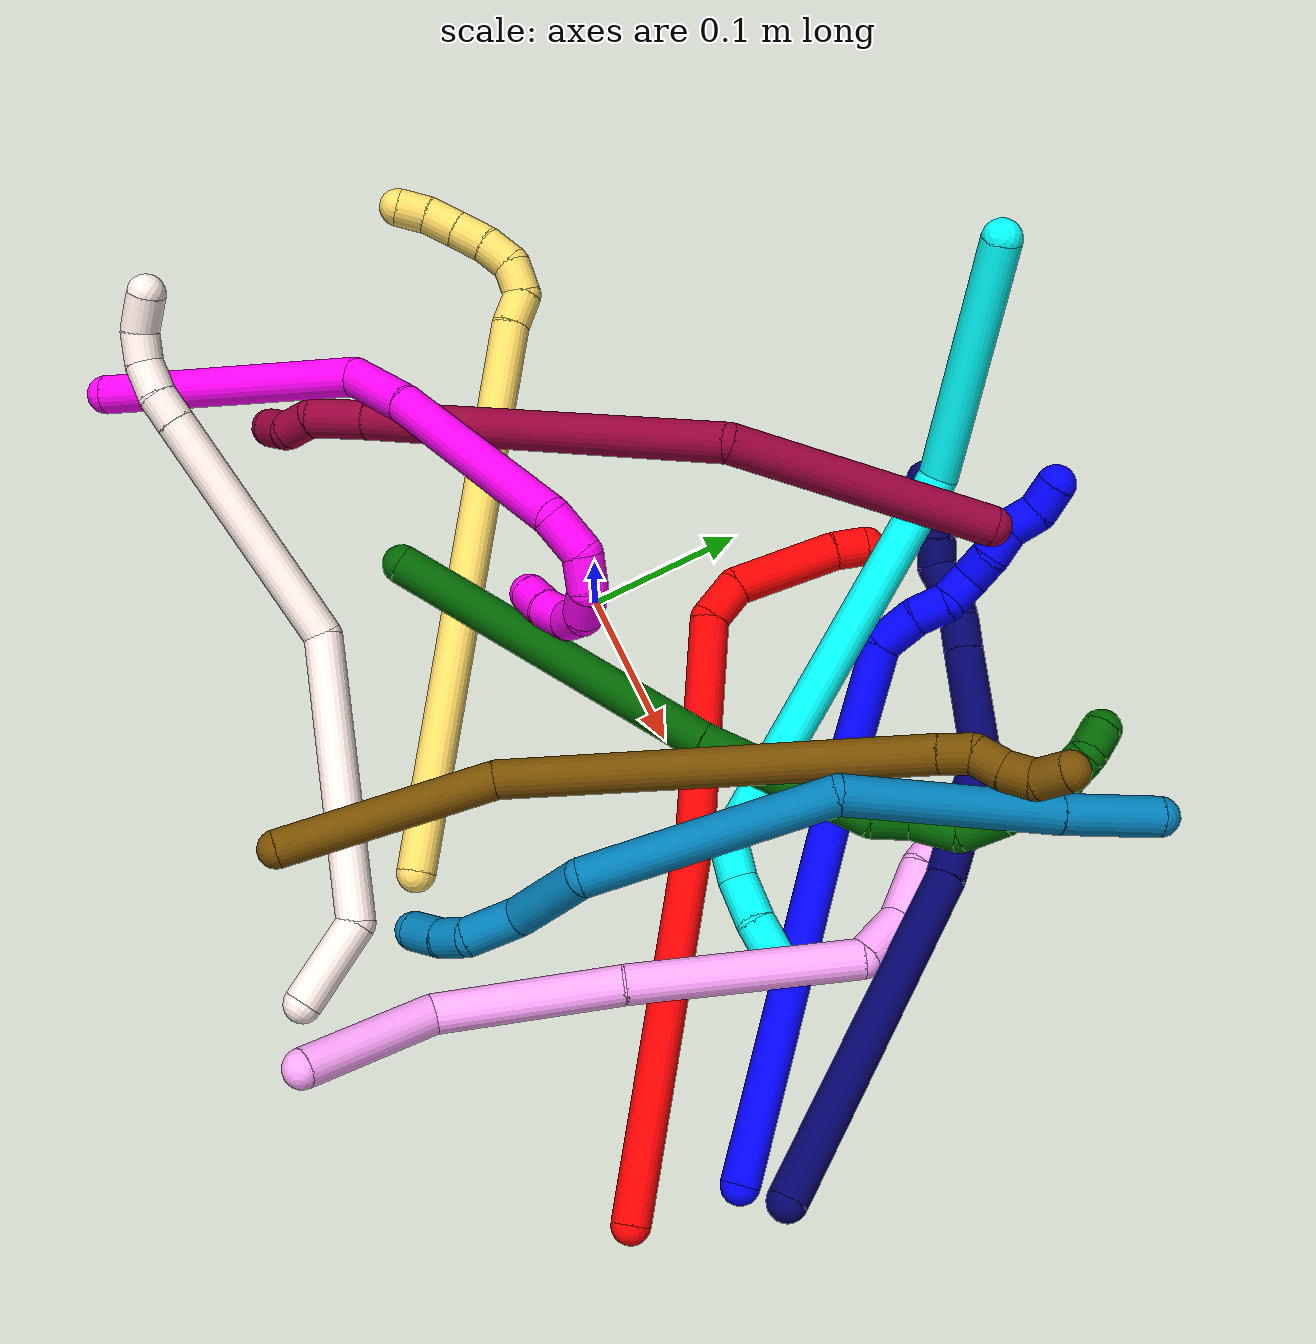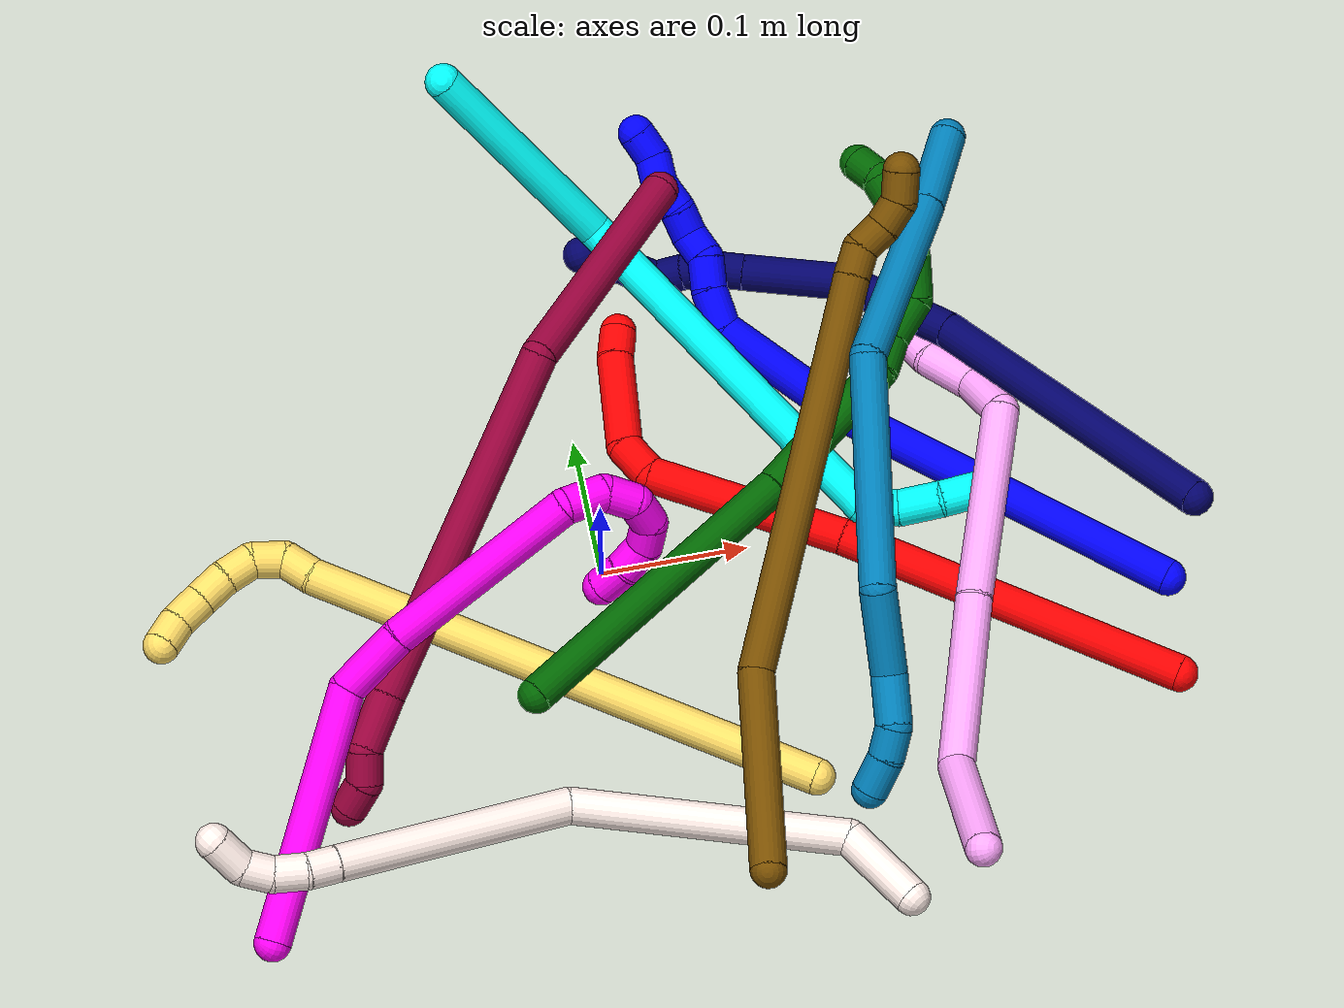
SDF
<sdf version="1.7">
 <world name="default">
  <plugin name="TubeGeneratorPlugin" filename="libtube_generator_plugin.so"/>
  <model name="photoneo_s_sensor">
   <static>1</static>
   <pose>0 0 2 1.57079 1.57079 3.14159</pose>
   <link name="link">
    <inertial><mass>0.1</mass></inertial>
    <sensor name="sensor" type="depth">
     <update_rate>30</update_rate>
     <camera>
      <horizontal_fov>1.22</horizontal_fov>
      <image><width>1920</width><height>1200</height><format>B8G8R8</format></image>
      <clip><near>0.1</near><far>4</far></clip>
      <depth_camera><output>points</output></depth_camera>
     </camera>
     <plugin name="camera_plugin" filename="libgazebo_ros_depth_camera.so">
      <baseline>0.2</baseline>
      <alwaysOn>1</alwaysOn>
      <updateRate>0.0</updateRate>
      <cameraName>camera_ir</cameraName>
      <imageTopicName>/camera/color/image_raw</imageTopicName>
      <cameraInfoTopicName>/camera/color/camera_info</cameraInfoTopicName>
      <depthImageTopicName>/camera/depth/image_raw</depthImageTopicName>
      <depthImageCameraInfoTopicName>/camera/depth/camera_info</depthImageCameraInfoTopicName>
      <pointCloudTopicName>/camera/depth/points</pointCloudTopicName>
      <frameName>fr_optical</frameName>
      <pointCloudCutoff>0.1</pointCloudCutoff>
      <pointCloudCutoffMax>2.0</pointCloudCutoffMax>
      <distortionK1>0</distortionK1>
      <distortionK2>0</distortionK2>
      <distortionK3>0</distortionK3>
      <distortionT1>0</distortionT1>
      <distortionT2>0</distortionT2>
      <CxPrime>0</CxPrime>
      <Cx>0</Cx>
      <Cy>0</Cy>
      <focalLength>0</focalLength>
      <hackBaseline>0</hackBaseline>
     </plugin>
    </sensor>
   </link>
  </model>
  <gravity>0 0 -9.8</gravity>
  <magnetic_field>6e-06 2.3e-05 -4.2e-05</magnetic_field>
  <atmosphere type="adiabatic"/>
  <physics name="default_physics" default="0" type="ode">
   <max_step_size>0.003</max_step_size>
   <real_time_factor>1</real_time_factor>
   <real_time_update_rate>1000</real_time_update_rate>
   <max_contacts>10000</max_contacts>
   <ode>
    <solver>
     <type>quick</type>
     <iters>100</iters>
     <sor>1.3</sor>
     <use_dynamic_moi_rescaling>0</use_dynamic_moi_rescaling>
    </solver>
    <constraints>
     <contact_max_correcting_vel>0</contact_max_correcting_vel>
     <contact_surface_layer>0.001</contact_surface_layer>
     <cfm>0</cfm>
     <erp>0.2</erp>
    </constraints>
   </ode>
  </physics>
  <scene><ambient>0.4 0.4 0.4 1</ambient><background>0.7 0.7 0.7 1</background><shadows>0</shadows></scene>
  <audio><device>default</device></audio>
  <spherical_coordinates>
   <surface_model>EARTH_WGS84</surface_model>
   <latitude_deg>0</latitude_deg>
   <longitude_deg>0</longitude_deg>
   <elevation>0</elevation>
   <heading_deg>0</heading_deg>
  </spherical_coordinates>
  <model name="bin">
   <static>1</static>
   <link name="bottom">
    <collision name="collision-bottom">
     <pose>0 0 -0.01 0 -0 0</pose>
     <geometry><box><size>0.8 0.6 0.02</size></box></geometry>
     <surface>
      <friction><ode><mu>100</mu><mu2>100</mu2></ode></friction>
      <contact><collide_bitmask>65535</collide_bitmask></contact>
     </surface>
    </collision>
   </link>
   <link name="west_wall">
    <collision name="collision-west_wall">
     <pose>-0.41 0 0.1 0 -0 0</pose>
     <geometry><box><size>0.02 0.6 0.2</size></box></geometry>
     <surface>
      <friction><ode><mu>100</mu><mu2>100</mu2></ode></friction>
      <contact><collide_bitmask>65535</collide_bitmask></contact>
     </surface>
    </collision>
   </link>
   <link name="east_wall">
    <collision name="collision-east_wall">
     <pose>0.41 0 0.1 0 -0 0</pose>
     <geometry><box><size>0.02 0.6 0.2</size></box></geometry>
     <surface>
      <friction><ode><mu>100</mu><mu2>100</mu2></ode></friction>
      <contact><collide_bitmask>65535</collide_bitmask></contact>
     </surface>
    </collision>
   </link>
   <link name="south_wall">
    <collision name="collision-south_wall">
     <pose>0 -0.31 0.1 0 -0 0</pose>
     <geometry><box><size>0.8 0.02 0.2</size></box></geometry>
     <surface>
      <friction><ode><mu>100</mu><mu2>100</mu2></ode></friction>
      <contact><collide_bitmask>65535</collide_bitmask></contact>
     </surface>
    </collision>
   </link>
   <link name="north_wall">
    <collision name="collision-north_wall">
     <pose>0 0.31 0.1 0 -0 0</pose>
     <geometry><box><size>0.8 0.02 0.2</size></box></geometry>
     <surface>
      <friction><ode><mu>100</mu><mu2>100</mu2></ode></friction>
      <contact><collide_bitmask>65535</collide_bitmask></contact>
     </surface>
    </collision>
   </link>
  </model>
  <model name="1">
   <static>0</static>
   <link name="1">
    <collision name="collision-cylinder-e_1_1_4">
     <pose>-0.033727 0.050159 0.108674 -0.432424 -0.274665 0.060692</pose>
     <geometry><cylinder><radius>0.0125</radius><length>0.248705</length></cylinder></geometry>
     <surface>
      <friction><ode><mu>1.16</mu><mu2>1.16</mu2><slip1>0</slip1><slip2>0</slip2></ode></friction>
      <contact><ode><kp>1e+06</kp><kd>1</kd><max_vel>0</max_vel><min_depth>0.001</min_depth></ode></contact>
     </surface>
    </collision>
    <visual name="visual-cylinder-e_1_1_4">
     <pose>-0.033727 0.050159 0.108674 -0.432424 -0.274665 0.060692</pose>
     <geometry><cylinder><radius>0.0125</radius><length>0.248705</length></cylinder></geometry>
     <material><ambient>0 0 1 1</ambient></material>
    </visual>
    <collision name="collision-cylinder-e_2_4_5">
     <pose>-0.095695 0.120194 0.253858 -0.498509 -0.596733 0.156252</pose>
     <geometry><cylinder><radius>0.0125</radius><length>0.100511</length></cylinder></geometry>
     <surface>
      <friction><ode><mu>1.16</mu><mu2>1.16</mu2><slip1>0</slip1><slip2>0</slip2></ode></friction>
      <contact><ode><kp>1e+06</kp><kd>1</kd><max_vel>0</max_vel><min_depth>0.001</min_depth></ode></contact>
     </surface>
    </collision>
    <visual name="visual-cylinder-e_2_4_5">
     <pose>-0.095695 0.120194 0.253858 -0.498509 -0.596733 0.156252</pose>
     <geometry><cylinder><radius>0.0125</radius><length>0.100511</length></cylinder></geometry>
     <material><ambient>0 0 1 1</ambient></material>
    </visual>
    <collision name="collision-cylinder-e_3_5_6">
     <pose>-0.133492 0.137189 0.300109 0.287463 -0.754891 -0.114631</pose>
     <geometry><cylinder><radius>0.0125</radius><length>0.027891</length></cylinder></geometry>
     <surface>
      <friction><ode><mu>1.16</mu><mu2>1.16</mu2><slip1>0</slip1><slip2>0</slip2></ode></friction>
      <contact><ode><kp>1e+06</kp><kd>1</kd><max_vel>0</max_vel><min_depth>0.001</min_depth></ode></contact>
     </surface>
    </collision>
    <visual name="visual-cylinder-e_3_5_6">
     <pose>-0.133492 0.137189 0.300109 0.287463 -0.754891 -0.114631</pose>
     <geometry><cylinder><radius>0.0125</radius><length>0.027891</length></cylinder></geometry>
     <material><ambient>0 0 1 1</ambient></material>
    </visual>
    <collision name="collision-cylinder-e_4_6_7">
     <pose>-0.15005 0.129547 0.316867 0.59625 -0.690233 -0.220047</pose>
     <geometry><cylinder><radius>0.0125</radius><length>0.021996</length></cylinder></geometry>
     <surface>
      <friction><ode><mu>1.16</mu><mu2>1.16</mu2><slip1>0</slip1><slip2>0</slip2></ode></friction>
      <contact><ode><kp>1e+06</kp><kd>1</kd><max_vel>0</max_vel><min_depth>0.001</min_depth></ode></contact>
     </surface>
    </collision>
    <visual name="visual-cylinder-e_4_6_7">
     <pose>-0.15005 0.129547 0.316867 0.59625 -0.690233 -0.220047</pose>
     <geometry><cylinder><radius>0.0125</radius><length>0.021996</length></cylinder></geometry>
     <material><ambient>0 0 1 1</ambient></material>
    </visual>
    <collision name="collision-cylinder-e_5_7_8">
     <pose>-0.160446 0.124032 0.333555 0.077716 -0.336514 -0.013207</pose>
     <geometry><cylinder><radius>0.0125</radius><length>0.020552</length></cylinder></geometry>
     <surface>
      <friction><ode><mu>1.16</mu><mu2>1.16</mu2><slip1>0</slip1><slip2>0</slip2></ode></friction>
      <contact><ode><kp>1e+06</kp><kd>1</kd><max_vel>0</max_vel><min_depth>0.001</min_depth></ode></contact>
     </surface>
    </collision>
    <visual name="visual-cylinder-e_5_7_8">
     <pose>-0.160446 0.124032 0.333555 0.077716 -0.336514 -0.013207</pose>
     <geometry><cylinder><radius>0.0125</radius><length>0.020552</length></cylinder></geometry>
     <material><ambient>0 0 1 1</ambient></material>
    </visual>
    <collision name="collision-cylinder-e_6_8_9">
     <pose>-0.172398 0.12299 0.34865 0.053269 -1.0053 -0.029289</pose>
     <geometry><cylinder><radius>0.0125</radius><length>0.020276</length></cylinder></geometry>
     <surface>
      <friction><ode><mu>1.16</mu><mu2>1.16</mu2><slip1>0</slip1><slip2>0</slip2></ode></friction>
      <contact><ode><kp>1e+06</kp><kd>1</kd><max_vel>0</max_vel><min_depth>0.001</min_depth></ode></contact>
     </surface>
    </collision>
    <visual name="visual-cylinder-e_6_8_9">
     <pose>-0.172398 0.12299 0.34865 0.053269 -1.0053 -0.029289</pose>
     <geometry><cylinder><radius>0.0125</radius><length>0.020276</length></cylinder></geometry>
     <material><ambient>0 0 1 1</ambient></material>
    </visual>
    <collision name="collision-cylinder-e_7_9_10">
     <pose>-0.187777 0.123659 0.361351 -0.130977 -0.748608 0.051513</pose>
     <geometry><cylinder><radius>0.0125</radius><length>0.020038</length></cylinder></geometry>
     <surface>
      <friction><ode><mu>1.16</mu><mu2>1.16</mu2><slip1>0</slip1><slip2>0</slip2></ode></friction>
      <contact><ode><kp>1e+06</kp><kd>1</kd><max_vel>0</max_vel><min_depth>0.001</min_depth></ode></contact>
     </surface>
    </collision>
    <visual name="visual-cylinder-e_7_9_10">
     <pose>-0.187777 0.123659 0.361351 -0.130977 -0.748608 0.051513</pose>
     <geometry><cylinder><radius>0.0125</radius><length>0.020038</length></cylinder></geometry>
     <material><ambient>0 0 1 1</ambient></material>
    </visual>
    <collision name="collision-cylinder-e_8_10_11">
     <pose>-0.200215 0.121117 0.376127 0.436827 -0.596457 -0.136245</pose>
     <geometry><cylinder><radius>0.0125</radius><length>0.020005</length></cylinder></geometry>
     <surface>
      <friction><ode><mu>1.16</mu><mu2>1.16</mu2><slip1>0</slip1><slip2>0</slip2></ode></friction>
      <contact><ode><kp>1e+06</kp><kd>1</kd><max_vel>0</max_vel><min_depth>0.001</min_depth></ode></contact>
     </surface>
    </collision>
    <visual name="visual-cylinder-e_8_10_11">
     <pose>-0.200215 0.121117 0.376127 0.436827 -0.596457 -0.136245</pose>
     <geometry><cylinder><radius>0.0125</radius><length>0.020005</length></cylinder></geometry>
     <material><ambient>0 0 1 1</ambient></material>
    </visual>
    <collision name="collision-cylinder-e_9_11_2">
     <pose>-0.213338 0.118682 0.390168 -0.161581 -0.847293 0.072992</pose>
     <geometry><cylinder><radius>0.0125</radius><length>0.020027</length></cylinder></geometry>
     <surface>
      <friction><ode><mu>1.16</mu><mu2>1.16</mu2><slip1>0</slip1><slip2>0</slip2></ode></friction>
      <contact><ode><kp>1e+06</kp><kd>1</kd><max_vel>0</max_vel><min_depth>0.001</min_depth></ode></contact>
     </surface>
    </collision>
    <visual name="visual-cylinder-e_9_11_2">
     <pose>-0.213338 0.118682 0.390168 -0.161581 -0.847293 0.072992</pose>
     <geometry><cylinder><radius>0.0125</radius><length>0.020027</length></cylinder></geometry>
     <material><ambient>0 0 1 1</ambient></material>
    </visual>
    <collision name="collision-sphere-2">
     <pose>-0.220843 0.119749 0.396711 0 -0 0</pose>
     <geometry><sphere><radius>0.0125</radius></sphere></geometry>
     <surface>
      <friction><ode><mu>1.16</mu><mu2>1.16</mu2><slip1>0</slip1><slip2>0</slip2></ode></friction>
      <contact><ode><kp>1e+06</kp><kd>1</kd><max_vel>0</max_vel><min_depth>0.001</min_depth></ode></contact>
     </surface>
    </collision>
    <visual name="visual-sphere-2">
     <pose>-0.220843 0.119749 0.396711 0 -0 0</pose>
     <geometry><sphere><radius>0.0125</radius></sphere></geometry>
     <material><ambient>0 0 1 1</ambient></material>
    </visual>
    <collision name="collision-sphere-11">
     <pose>-0.205833 0.117616 0.383625 0 -0 0</pose>
     <geometry><sphere><radius>0.0125</radius></sphere></geometry>
     <surface>
      <friction><ode><mu>1.16</mu><mu2>1.16</mu2><slip1>0</slip1><slip2>0</slip2></ode></friction>
      <contact><ode><kp>1e+06</kp><kd>1</kd><max_vel>0</max_vel><min_depth>0.001</min_depth></ode></contact>
     </surface>
    </collision>
    <visual name="visual-sphere-11">
     <pose>-0.205833 0.117616 0.383625 0 -0 0</pose>
     <geometry><sphere><radius>0.0125</radius></sphere></geometry>
     <material><ambient>0 0 1 1</ambient></material>
    </visual>
    <collision name="collision-sphere-10">
     <pose>-0.194596 0.124618 0.368629 0 -0 0</pose>
     <geometry><sphere><radius>0.0125</radius></sphere></geometry>
     <surface>
      <friction><ode><mu>1.16</mu><mu2>1.16</mu2><slip1>0</slip1><slip2>0</slip2></ode></friction>
      <contact><ode><kp>1e+06</kp><kd>1</kd><max_vel>0</max_vel><min_depth>0.001</min_depth></ode></contact>
     </surface>
    </collision>
    <visual name="visual-sphere-10">
     <pose>-0.194596 0.124618 0.368629 0 -0 0</pose>
     <geometry><sphere><radius>0.0125</radius></sphere></geometry>
     <material><ambient>0 0 1 1</ambient></material>
    </visual>
    <collision name="collision-sphere-9">
     <pose>-0.180958 0.122701 0.354074 0 -0 0</pose>
     <geometry><sphere><radius>0.0125</radius></sphere></geometry>
     <surface>
      <friction><ode><mu>1.16</mu><mu2>1.16</mu2><slip1>0</slip1><slip2>0</slip2></ode></friction>
      <contact><ode><kp>1e+06</kp><kd>1</kd><max_vel>0</max_vel><min_depth>0.001</min_depth></ode></contact>
     </surface>
    </collision>
    <visual name="visual-sphere-9">
     <pose>-0.180958 0.122701 0.354074 0 -0 0</pose>
     <geometry><sphere><radius>0.0125</radius></sphere></geometry>
     <material><ambient>0 0 1 1</ambient></material>
    </visual>
    <collision name="collision-sphere-4">
     <pose>-0.067455 0.100319 0.217348 0 -0 0</pose>
     <geometry><sphere><radius>0.0125</radius></sphere></geometry>
     <surface>
      <friction><ode><mu>1.16</mu><mu2>1.16</mu2><slip1>0</slip1><slip2>0</slip2></ode></friction>
      <contact><ode><kp>1e+06</kp><kd>1</kd><max_vel>0</max_vel><min_depth>0.001</min_depth></ode></contact>
     </surface>
    </collision>
    <visual name="visual-sphere-4">
     <pose>-0.067455 0.100319 0.217348 0 -0 0</pose>
     <geometry><sphere><radius>0.0125</radius></sphere></geometry>
     <material><ambient>0 0 1 1</ambient></material>
    </visual>
    <collision name="collision-sphere-1">
     <geometry><sphere><radius>0.0125</radius></sphere></geometry>
     <surface>
      <friction><ode><mu>1.16</mu><mu2>1.16</mu2><slip1>0</slip1><slip2>0</slip2></ode></friction>
      <contact><ode><kp>1e+06</kp><kd>1</kd><max_vel>0</max_vel><min_depth>0.001</min_depth></ode></contact>
     </surface>
    </collision>
    <visual name="visual-sphere-1">
     <geometry><sphere><radius>0.0125</radius></sphere></geometry>
     <material><ambient>0 0 1 1</ambient></material>
    </visual>
    <collision name="collision-sphere-8">
     <pose>-0.163839 0.123279 0.343225 0 -0 0</pose>
     <geometry><sphere><radius>0.0125</radius></sphere></geometry>
     <surface>
      <friction><ode><mu>1.16</mu><mu2>1.16</mu2><slip1>0</slip1><slip2>0</slip2></ode></friction>
      <contact><ode><kp>1e+06</kp><kd>1</kd><max_vel>0</max_vel><min_depth>0.001</min_depth></ode></contact>
     </surface>
    </collision>
    <visual name="visual-sphere-8">
     <pose>-0.163839 0.123279 0.343225 0 -0 0</pose>
     <geometry><sphere><radius>0.0125</radius></sphere></geometry>
     <material><ambient>0 0 1 1</ambient></material>
    </visual>
    <collision name="collision-sphere-5">
     <pose>-0.123936 0.140069 0.290369 0 -0 0</pose>
     <geometry><sphere><radius>0.0125</radius></sphere></geometry>
     <surface>
      <friction><ode><mu>1.16</mu><mu2>1.16</mu2><slip1>0</slip1><slip2>0</slip2></ode></friction>
      <contact><ode><kp>1e+06</kp><kd>1</kd><max_vel>0</max_vel><min_depth>0.001</min_depth></ode></contact>
     </surface>
    </collision>
    <visual name="visual-sphere-5">
     <pose>-0.123936 0.140069 0.290369 0 -0 0</pose>
     <geometry><sphere><radius>0.0125</radius></sphere></geometry>
     <material><ambient>0 0 1 1</ambient></material>
    </visual>
    <collision name="collision-sphere-6">
     <pose>-0.143047 0.13431 0.30985 0 -0 0</pose>
     <geometry><sphere><radius>0.0125</radius></sphere></geometry>
     <surface>
      <friction><ode><mu>1.16</mu><mu2>1.16</mu2><slip1>0</slip1><slip2>0</slip2></ode></friction>
      <contact><ode><kp>1e+06</kp><kd>1</kd><max_vel>0</max_vel><min_depth>0.001</min_depth></ode></contact>
     </surface>
    </collision>
    <visual name="visual-sphere-6">
     <pose>-0.143047 0.13431 0.30985 0 -0 0</pose>
     <geometry><sphere><radius>0.0125</radius></sphere></geometry>
     <material><ambient>0 0 1 1</ambient></material>
    </visual>
    <collision name="collision-sphere-7">
     <pose>-0.157053 0.124785 0.323884 0 -0 0</pose>
     <geometry><sphere><radius>0.0125</radius></sphere></geometry>
     <surface>
      <friction><ode><mu>1.16</mu><mu2>1.16</mu2><slip1>0</slip1><slip2>0</slip2></ode></friction>
      <contact><ode><kp>1e+06</kp><kd>1</kd><max_vel>0</max_vel><min_depth>0.001</min_depth></ode></contact>
     </surface>
    </collision>
    <visual name="visual-sphere-7">
     <pose>-0.157053 0.124785 0.323884 0 -0 0</pose>
     <geometry><sphere><radius>0.0125</radius></sphere></geometry>
     <material><ambient>0 0 1 1</ambient></material>
    </visual>
    <inertial>
     <pose>-0.087728 0.087104 0.208774 0 -0 0</pose>
     <mass>0.5</mass>
     <inertia>
      <ixx>0.001391</ixx>
      <ixy>0</ixy>
      <ixz>0</ixz>
      <iyy>0.001367</iyy>
      <iyz>0</iyz>
      <izz>-0.000115</izz>
     </inertia>
    </inertial>
   </link>
   <pose>0.370835 -0.082846 0.012449 2.90025 1.21988 -1.36146</pose>
  </model>
  <model name="2">
   <static>0</static>
   <link name="2">
    <collision name="collision-cylinder-e_1_1_4">
     <pose>-0.086972 0.040466 -0.076213 -2.65348 -0.789337 2.06392</pose>
     <geometry><cylinder><radius>0.0125</radius><length>0.24503</length></cylinder></geometry>
     <surface>
      <friction><ode><mu>1.16</mu><mu2>1.16</mu2><slip1>0</slip1><slip2>0</slip2></ode></friction>
      <contact><ode><kp>1e+06</kp><kd>1</kd><max_vel>0</max_vel><min_depth>0.001</min_depth></ode></contact>
     </surface>
    </collision>
    <visual name="visual-cylinder-e_1_1_4">
     <pose>-0.086972 0.040466 -0.076213 -2.65348 -0.789337 2.06392</pose>
     <geometry><cylinder><radius>0.0125</radius><length>0.24503</length></cylinder></geometry>
     <material><ambient>1 0 0 1</ambient></material>
    </visual>
    <collision name="collision-cylinder-e_2_4_5">
     <pose>-0.227381 0.100916 -0.190666 -2.66005 -0.891535 2.19227</pose>
     <geometry><cylinder><radius>0.0125</radius><length>0.137364</length></cylinder></geometry>
     <surface>
      <friction><ode><mu>1.16</mu><mu2>1.16</mu2><slip1>0</slip1><slip2>0</slip2></ode></friction>
      <contact><ode><kp>1e+06</kp><kd>1</kd><max_vel>0</max_vel><min_depth>0.001</min_depth></ode></contact>
     </surface>
    </collision>
    <visual name="visual-cylinder-e_2_4_5">
     <pose>-0.227381 0.100916 -0.190666 -2.66005 -0.891535 2.19227</pose>
     <geometry><cylinder><radius>0.0125</radius><length>0.137364</length></cylinder></geometry>
     <material><ambient>1 0 0 1</ambient></material>
    </visual>
    <collision name="collision-cylinder-e_3_5_6">
     <pose>-0.284825 0.12803 -0.240669 -2.59665 -0.283482 0.944322</pose>
     <geometry><cylinder><radius>0.0125</radius><length>0.028653</length></cylinder></geometry>
     <surface>
      <friction><ode><mu>1.16</mu><mu2>1.16</mu2><slip1>0</slip1><slip2>0</slip2></ode></friction>
      <contact><ode><kp>1e+06</kp><kd>1</kd><max_vel>0</max_vel><min_depth>0.001</min_depth></ode></contact>
     </surface>
    </collision>
    <visual name="visual-cylinder-e_3_5_6">
     <pose>-0.284825 0.12803 -0.240669 -2.59665 -0.283482 0.944322</pose>
     <geometry><cylinder><radius>0.0125</radius><length>0.028653</length></cylinder></geometry>
     <material><ambient>1 0 0 1</ambient></material>
    </visual>
    <collision name="collision-cylinder-e_4_6_7">
     <pose>-0.281585 0.159425 -0.27521 -2.3246 0.214396 -0.487345</pose>
     <geometry><cylinder><radius>0.0125</radius><length>0.068124</length></cylinder></geometry>
     <surface>
      <friction><ode><mu>1.16</mu><mu2>1.16</mu2><slip1>0</slip1><slip2>0</slip2></ode></friction>
      <contact><ode><kp>1e+06</kp><kd>1</kd><max_vel>0</max_vel><min_depth>0.001</min_depth></ode></contact>
     </surface>
    </collision>
    <visual name="visual-cylinder-e_4_6_7">
     <pose>-0.281585 0.159425 -0.27521 -2.3246 0.214396 -0.487345</pose>
     <geometry><cylinder><radius>0.0125</radius><length>0.068124</length></cylinder></geometry>
     <material><ambient>1 0 0 1</ambient></material>
    </visual>
    <collision name="collision-cylinder-e_5_7_2">
     <pose>-0.270321 0.191007 -0.304217 -2.27602 0.395975 -0.819334</pose>
     <geometry><cylinder><radius>0.0125</radius><length>0.020829</length></cylinder></geometry>
     <surface>
      <friction><ode><mu>1.16</mu><mu2>1.16</mu2><slip1>0</slip1><slip2>0</slip2></ode></friction>
      <contact><ode><kp>1e+06</kp><kd>1</kd><max_vel>0</max_vel><min_depth>0.001</min_depth></ode></contact>
     </surface>
    </collision>
    <visual name="visual-cylinder-e_5_7_2">
     <pose>-0.270321 0.191007 -0.304217 -2.27602 0.395975 -0.819334</pose>
     <geometry><cylinder><radius>0.0125</radius><length>0.020829</length></cylinder></geometry>
     <material><ambient>1 0 0 1</ambient></material>
    </visual>
    <collision name="collision-sphere-2">
     <pose>-0.266304 0.198324 -0.310445 0 -0 0</pose>
     <geometry><sphere><radius>0.0125</radius></sphere></geometry>
     <surface>
      <friction><ode><mu>1.16</mu><mu2>1.16</mu2><slip1>0</slip1><slip2>0</slip2></ode></friction>
      <contact><ode><kp>1e+06</kp><kd>1</kd><max_vel>0</max_vel><min_depth>0.001</min_depth></ode></contact>
     </surface>
    </collision>
    <visual name="visual-sphere-2">
     <pose>-0.266304 0.198324 -0.310445 0 -0 0</pose>
     <geometry><sphere><radius>0.0125</radius></sphere></geometry>
     <material><ambient>1 0 0 1</ambient></material>
    </visual>
    <collision name="collision-sphere-7">
     <pose>-0.274338 0.183691 -0.297989 0 -0 0</pose>
     <geometry><sphere><radius>0.0125</radius></sphere></geometry>
     <surface>
      <friction><ode><mu>1.16</mu><mu2>1.16</mu2><slip1>0</slip1><slip2>0</slip2></ode></friction>
      <contact><ode><kp>1e+06</kp><kd>1</kd><max_vel>0</max_vel><min_depth>0.001</min_depth></ode></contact>
     </surface>
    </collision>
    <visual name="visual-sphere-7">
     <pose>-0.274338 0.183691 -0.297989 0 -0 0</pose>
     <geometry><sphere><radius>0.0125</radius></sphere></geometry>
     <material><ambient>1 0 0 1</ambient></material>
    </visual>
    <collision name="collision-sphere-6">
     <pose>-0.288832 0.135159 -0.252431 0 -0 0</pose>
     <geometry><sphere><radius>0.0125</radius></sphere></geometry>
     <surface>
      <friction><ode><mu>1.16</mu><mu2>1.16</mu2><slip1>0</slip1><slip2>0</slip2></ode></friction>
      <contact><ode><kp>1e+06</kp><kd>1</kd><max_vel>0</max_vel><min_depth>0.001</min_depth></ode></contact>
     </surface>
    </collision>
    <visual name="visual-sphere-6">
     <pose>-0.288832 0.135159 -0.252431 0 -0 0</pose>
     <geometry><sphere><radius>0.0125</radius></sphere></geometry>
     <material><ambient>1 0 0 1</ambient></material>
    </visual>
    <collision name="collision-sphere-5">
     <pose>-0.280818 0.1209 -0.228907 0 -0 0</pose>
     <geometry><sphere><radius>0.0125</radius></sphere></geometry>
     <surface>
      <friction><ode><mu>1.16</mu><mu2>1.16</mu2><slip1>0</slip1><slip2>0</slip2></ode></friction>
      <contact><ode><kp>1e+06</kp><kd>1</kd><max_vel>0</max_vel><min_depth>0.001</min_depth></ode></contact>
     </surface>
    </collision>
    <visual name="visual-sphere-5">
     <pose>-0.280818 0.1209 -0.228907 0 -0 0</pose>
     <geometry><sphere><radius>0.0125</radius></sphere></geometry>
     <material><ambient>1 0 0 1</ambient></material>
    </visual>
    <collision name="collision-sphere-1">
     <geometry><sphere><radius>0.0125</radius></sphere></geometry>
     <surface>
      <friction><ode><mu>1.16</mu><mu2>1.16</mu2><slip1>0</slip1><slip2>0</slip2></ode></friction>
      <contact><ode><kp>1e+06</kp><kd>1</kd><max_vel>0</max_vel><min_depth>0.001</min_depth></ode></contact>
     </surface>
    </collision>
    <visual name="visual-sphere-1">
     <geometry><sphere><radius>0.0125</radius></sphere></geometry>
     <material><ambient>1 0 0 1</ambient></material>
    </visual>
    <collision name="collision-sphere-4">
     <pose>-0.173943 0.080932 -0.152425 0 -0 0</pose>
     <geometry><sphere><radius>0.0125</radius></sphere></geometry>
     <surface>
      <friction><ode><mu>1.16</mu><mu2>1.16</mu2><slip1>0</slip1><slip2>0</slip2></ode></friction>
      <contact><ode><kp>1e+06</kp><kd>1</kd><max_vel>0</max_vel><min_depth>0.001</min_depth></ode></contact>
     </surface>
    </collision>
    <visual name="visual-sphere-4">
     <pose>-0.173943 0.080932 -0.152425 0 -0 0</pose>
     <geometry><sphere><radius>0.0125</radius></sphere></geometry>
     <material><ambient>1 0 0 1</ambient></material>
    </visual>
    <inertial>
     <pose>-0.171038 0.08457 -0.153692 0 -0 0</pose>
     <mass>0.5</mass>
     <inertia>
      <ixx>0.000382</ixx>
      <ixy>0</ixy>
      <ixz>0</ixz>
      <iyy>0.001924</iyy>
      <iyz>0</iyz>
      <izz>0.000523</izz>
     </inertia>
    </inertial>
   </link>
   <pose>0.362669 -0.153246 0.011499 0.803013 0.267299 0.119262</pose>
  </model>
  <model name="3">
   <static>0</static>
   <link name="3">
    <collision name="collision-cylinder-e_1_1_4">
     <pose>0.060067 -0.028715 0.042455 0.594686 0.864403 0.280842</pose>
     <geometry><cylinder><radius>0.0125</radius><length>0.157924</length></cylinder></geometry>
     <surface>
      <friction><ode><mu>1.16</mu><mu2>1.16</mu2><slip1>0</slip1><slip2>0</slip2></ode></friction>
      <contact><ode><kp>1e+06</kp><kd>1</kd><max_vel>0</max_vel><min_depth>0.001</min_depth></ode></contact>
     </surface>
    </collision>
    <visual name="visual-cylinder-e_1_1_4">
     <pose>0.060067 -0.028715 0.042455 0.594686 0.864403 0.280842</pose>
     <geometry><cylinder><radius>0.0125</radius><length>0.157924</length></cylinder></geometry>
     <material><ambient>0.003922 1 0.996078 1</ambient></material>
    </visual>
    <collision name="collision-cylinder-e_2_4_5">
     <pose>0.240037 -0.110522 0.077009 1.71852 1.14988 1.28895</pose>
     <geometry><cylinder><radius>0.0125</radius><length>0.262739</length></cylinder></geometry>
     <surface>
      <friction><ode><mu>1.16</mu><mu2>1.16</mu2><slip1>0</slip1><slip2>0</slip2></ode></friction>
      <contact><ode><kp>1e+06</kp><kd>1</kd><max_vel>0</max_vel><min_depth>0.001</min_depth></ode></contact>
     </surface>
    </collision>
    <visual name="visual-cylinder-e_2_4_5">
     <pose>0.240037 -0.110522 0.077009 1.71852 1.14988 1.28895</pose>
     <geometry><cylinder><radius>0.0125</radius><length>0.262739</length></cylinder></geometry>
     <material><ambient>0.003922 1 0.996078 1</ambient></material>
    </visual>
    <collision name="collision-cylinder-e_3_5_6">
     <pose>0.364477 -0.174478 0.070447 1.44819 0.392929 0.348455</pose>
     <geometry><cylinder><radius>0.0125</radius><length>0.023697</length></cylinder></geometry>
     <surface>
      <friction><ode><mu>1.16</mu><mu2>1.16</mu2><slip1>0</slip1><slip2>0</slip2></ode></friction>
      <contact><ode><kp>1e+06</kp><kd>1</kd><max_vel>0</max_vel><min_depth>0.001</min_depth></ode></contact>
     </surface>
    </collision>
    <visual name="visual-cylinder-e_3_5_6">
     <pose>0.364477 -0.174478 0.070447 1.44819 0.392929 0.348455</pose>
     <geometry><cylinder><radius>0.0125</radius><length>0.023697</length></cylinder></geometry>
     <material><ambient>0.003922 1 0.996078 1</ambient></material>
    </visual>
    <collision name="collision-cylinder-e_4_6_7">
     <pose>0.371207 -0.200186 0.069565 1.71924 0.145094 0.168304</pose>
     <geometry><cylinder><radius>0.0125</radius><length>0.030338</length></cylinder></geometry>
     <surface>
      <friction><ode><mu>1.16</mu><mu2>1.16</mu2><slip1>0</slip1><slip2>0</slip2></ode></friction>
      <contact><ode><kp>1e+06</kp><kd>1</kd><max_vel>0</max_vel><min_depth>0.001</min_depth></ode></contact>
     </surface>
    </collision>
    <visual name="visual-cylinder-e_4_6_7">
     <pose>0.371207 -0.200186 0.069565 1.71924 0.145094 0.168304</pose>
     <geometry><cylinder><radius>0.0125</radius><length>0.030338</length></cylinder></geometry>
     <material><ambient>0.003922 1 0.996078 1</ambient></material>
    </visual>
    <collision name="collision-cylinder-e_5_7_2">
     <pose>0.374601 -0.227612 0.067911 1.52586 0.095063 0.090891</pose>
     <geometry><cylinder><radius>0.0125</radius><length>0.025301</length></cylinder></geometry>
     <surface>
      <friction><ode><mu>1.16</mu><mu2>1.16</mu2><slip1>0</slip1><slip2>0</slip2></ode></friction>
      <contact><ode><kp>1e+06</kp><kd>1</kd><max_vel>0</max_vel><min_depth>0.001</min_depth></ode></contact>
     </surface>
    </collision>
    <visual name="visual-cylinder-e_5_7_2">
     <pose>0.374601 -0.227612 0.067911 1.52586 0.095063 0.090891</pose>
     <geometry><cylinder><radius>0.0125</radius><length>0.025301</length></cylinder></geometry>
     <material><ambient>0.003922 1 0.996078 1</ambient></material>
    </visual>
    <collision name="collision-sphere-2">
     <pose>0.375802 -0.240192 0.068477 0 -0 0</pose>
     <geometry><sphere><radius>0.0125</radius></sphere></geometry>
     <surface>
      <friction><ode><mu>1.16</mu><mu2>1.16</mu2><slip1>0</slip1><slip2>0</slip2></ode></friction>
      <contact><ode><kp>1e+06</kp><kd>1</kd><max_vel>0</max_vel><min_depth>0.001</min_depth></ode></contact>
     </surface>
    </collision>
    <visual name="visual-sphere-2">
     <pose>0.375802 -0.240192 0.068477 0 -0 0</pose>
     <geometry><sphere><radius>0.0125</radius></sphere></geometry>
     <material><ambient>0.003922 1 0.996078 1</ambient></material>
    </visual>
    <collision name="collision-sphere-7">
     <pose>0.3734 -0.215031 0.067345 0 -0 0</pose>
     <geometry><sphere><radius>0.0125</radius></sphere></geometry>
     <surface>
      <friction><ode><mu>1.16</mu><mu2>1.16</mu2><slip1>0</slip1><slip2>0</slip2></ode></friction>
      <contact><ode><kp>1e+06</kp><kd>1</kd><max_vel>0</max_vel><min_depth>0.001</min_depth></ode></contact>
     </surface>
    </collision>
    <visual name="visual-sphere-7">
     <pose>0.3734 -0.215031 0.067345 0 -0 0</pose>
     <geometry><sphere><radius>0.0125</radius></sphere></geometry>
     <material><ambient>0.003922 1 0.996078 1</ambient></material>
    </visual>
    <collision name="collision-sphere-6">
     <pose>0.369014 -0.185342 0.071785 0 -0 0</pose>
     <geometry><sphere><radius>0.0125</radius></sphere></geometry>
     <surface>
      <friction><ode><mu>1.16</mu><mu2>1.16</mu2><slip1>0</slip1><slip2>0</slip2></ode></friction>
      <contact><ode><kp>1e+06</kp><kd>1</kd><max_vel>0</max_vel><min_depth>0.001</min_depth></ode></contact>
     </surface>
    </collision>
    <visual name="visual-sphere-6">
     <pose>0.369014 -0.185342 0.071785 0 -0 0</pose>
     <geometry><sphere><radius>0.0125</radius></sphere></geometry>
     <material><ambient>0.003922 1 0.996078 1</ambient></material>
    </visual>
    <collision name="collision-sphere-5">
     <pose>0.35994 -0.163615 0.069108 0 -0 0</pose>
     <geometry><sphere><radius>0.0125</radius></sphere></geometry>
     <surface>
      <friction><ode><mu>1.16</mu><mu2>1.16</mu2><slip1>0</slip1><slip2>0</slip2></ode></friction>
      <contact><ode><kp>1e+06</kp><kd>1</kd><max_vel>0</max_vel><min_depth>0.001</min_depth></ode></contact>
     </surface>
    </collision>
    <visual name="visual-sphere-5">
     <pose>0.35994 -0.163615 0.069108 0 -0 0</pose>
     <geometry><sphere><radius>0.0125</radius></sphere></geometry>
     <material><ambient>0.003922 1 0.996078 1</ambient></material>
    </visual>
    <collision name="collision-sphere-1">
     <geometry><sphere><radius>0.0125</radius></sphere></geometry>
     <surface>
      <friction><ode><mu>1.16</mu><mu2>1.16</mu2><slip1>0</slip1><slip2>0</slip2></ode></friction>
      <contact><ode><kp>1e+06</kp><kd>1</kd><max_vel>0</max_vel><min_depth>0.001</min_depth></ode></contact>
     </surface>
    </collision>
    <visual name="visual-sphere-1">
     <geometry><sphere><radius>0.0125</radius></sphere></geometry>
     <material><ambient>0.003922 1 0.996078 1</ambient></material>
    </visual>
    <collision name="collision-sphere-4">
     <pose>0.120134 -0.05743 0.08491 0 -0 0</pose>
     <geometry><sphere><radius>0.0125</radius></sphere></geometry>
     <surface>
      <friction><ode><mu>1.16</mu><mu2>1.16</mu2><slip1>0</slip1><slip2>0</slip2></ode></friction>
      <contact><ode><kp>1e+06</kp><kd>1</kd><max_vel>0</max_vel><min_depth>0.001</min_depth></ode></contact>
     </surface>
    </collision>
    <visual name="visual-sphere-4">
     <pose>0.120134 -0.05743 0.08491 0 -0 0</pose>
     <geometry><sphere><radius>0.0125</radius></sphere></geometry>
     <material><ambient>0.003922 1 0.996078 1</ambient></material>
    </visual>
    <inertial>
     <pose>0.20386 -0.09908 0.064872 0 -0 0</pose>
     <mass>0.5</mass>
     <inertia>
      <ixx>0.001077</ixx>
      <ixy>0</ixy>
      <ixz>0</ixz>
      <iyy>0.002203</iyy>
      <iyz>0</iyz>
      <izz>-0.000895</izz>
     </inertia>
    </inertial>
   </link>
   <pose>-0.048997 0.288097 0.189167 -2.93552 0.38466 -1.3883</pose>
  </model>
  <model name="4">
   <static>0</static>
   <link name="4">
    <collision name="collision-cylinder-e_1_1_4">
     <pose>0.016731 0.029963 -0.029834 -2.35405 0.376783 -0.860432</pose>
     <geometry><cylinder><radius>0.0125</radius><length>0.090945</length></cylinder></geometry>
     <surface>
      <friction><ode><mu>1.16</mu><mu2>1.16</mu2><slip1>0</slip1><slip2>0</slip2></ode></friction>
      <contact><ode><kp>1e+06</kp><kd>1</kd><max_vel>0</max_vel><min_depth>0.001</min_depth></ode></contact>
     </surface>
    </collision>
    <visual name="visual-cylinder-e_1_1_4">
     <pose>0.016731 0.029963 -0.029834 -2.35405 0.376783 -0.860432</pose>
     <geometry><cylinder><radius>0.0125</radius><length>0.090945</length></cylinder></geometry>
     <material><ambient>1 0.65098 0.996078 1</ambient></material>
    </visual>
    <collision name="collision-cylinder-e_2_4_5">
     <pose>0.041978 0.117792 -0.067216 -1.70049 0.144914 -0.164955</pose>
     <geometry><cylinder><radius>0.0125</radius><length>0.117951</length></cylinder></geometry>
     <surface>
      <friction><ode><mu>1.16</mu><mu2>1.16</mu2><slip1>0</slip1><slip2>0</slip2></ode></friction>
      <contact><ode><kp>1e+06</kp><kd>1</kd><max_vel>0</max_vel><min_depth>0.001</min_depth></ode></contact>
     </surface>
    </collision>
    <visual name="visual-cylinder-e_2_4_5">
     <pose>0.041978 0.117792 -0.067216 -1.70049 0.144914 -0.164955</pose>
     <geometry><cylinder><radius>0.0125</radius><length>0.117951</length></cylinder></geometry>
     <material><ambient>1 0.65098 0.996078 1</ambient></material>
    </visual>
    <collision name="collision-cylinder-e_3_5_6">
     <pose>0.069928 0.244229 -0.088705 -1.7714 0.270899 -0.330525</pose>
     <geometry><cylinder><radius>0.0125</radius><length>0.14524</length></cylinder></geometry>
     <surface>
      <friction><ode><mu>1.16</mu><mu2>1.16</mu2><slip1>0</slip1><slip2>0</slip2></ode></friction>
      <contact><ode><kp>1e+06</kp><kd>1</kd><max_vel>0</max_vel><min_depth>0.001</min_depth></ode></contact>
     </surface>
    </collision>
    <visual name="visual-cylinder-e_3_5_6">
     <pose>0.069928 0.244229 -0.088705 -1.7714 0.270899 -0.330525</pose>
     <geometry><cylinder><radius>0.0125</radius><length>0.14524</length></cylinder></geometry>
     <material><ambient>1 0.65098 0.996078 1</ambient></material>
    </visual>
    <collision name="collision-cylinder-e_4_6_7">
     <pose>0.092234 0.32343 -0.118816 -2.55987 0.14741 -0.483674</pose>
     <geometry><cylinder><radius>0.0125</radius><length>0.039127</length></cylinder></geometry>
     <surface>
      <friction><ode><mu>1.16</mu><mu2>1.16</mu2><slip1>0</slip1><slip2>0</slip2></ode></friction>
      <contact><ode><kp>1e+06</kp><kd>1</kd><max_vel>0</max_vel><min_depth>0.001</min_depth></ode></contact>
     </surface>
    </collision>
    <visual name="visual-cylinder-e_4_6_7">
     <pose>0.092234 0.32343 -0.118816 -2.55987 0.14741 -0.483674</pose>
     <geometry><cylinder><radius>0.0125</radius><length>0.039127</length></cylinder></geometry>
     <material><ambient>1 0.65098 0.996078 1</ambient></material>
    </visual>
    <collision name="collision-cylinder-e_5_7_8">
     <pose>0.09007 0.342444 -0.151599 -2.67441 -0.264346 1.01909</pose>
     <geometry><cylinder><radius>0.0125</radius><length>0.038558</length></cylinder></geometry>
     <surface>
      <friction><ode><mu>1.16</mu><mu2>1.16</mu2><slip1>0</slip1><slip2>0</slip2></ode></friction>
      <contact><ode><kp>1e+06</kp><kd>1</kd><max_vel>0</max_vel><min_depth>0.001</min_depth></ode></contact>
     </surface>
    </collision>
    <visual name="visual-cylinder-e_5_7_8">
     <pose>0.09007 0.342444 -0.151599 -2.67441 -0.264346 1.01909</pose>
     <geometry><cylinder><radius>0.0125</radius><length>0.038558</length></cylinder></geometry>
     <material><ambient>1 0.65098 0.996078 1</ambient></material>
    </visual>
    <collision name="collision-cylinder-e_6_8_9">
     <pose>0.084448 0.357917 -0.177375 -2.48284 -0.050456 0.147369</pose>
     <geometry><cylinder><radius>0.0125</radius><length>0.023199</length></cylinder></geometry>
     <surface>
      <friction><ode><mu>1.16</mu><mu2>1.16</mu2><slip1>0</slip1><slip2>0</slip2></ode></friction>
      <contact><ode><kp>1e+06</kp><kd>1</kd><max_vel>0</max_vel><min_depth>0.001</min_depth></ode></contact>
     </surface>
    </collision>
    <visual name="visual-cylinder-e_6_8_9">
     <pose>0.084448 0.357917 -0.177375 -2.48284 -0.050456 0.147369</pose>
     <geometry><cylinder><radius>0.0125</radius><length>0.023199</length></cylinder></geometry>
     <material><ambient>1 0.65098 0.996078 1</ambient></material>
    </visual>
    <collision name="collision-cylinder-e_7_9_2">
     <pose>0.081243 0.380749 -0.202383 -2.35955 -0.116754 0.281656</pose>
     <geometry><cylinder><radius>0.0125</radius><length>0.044979</length></cylinder></geometry>
     <surface>
      <friction><ode><mu>1.16</mu><mu2>1.16</mu2><slip1>0</slip1><slip2>0</slip2></ode></friction>
      <contact><ode><kp>1e+06</kp><kd>1</kd><max_vel>0</max_vel><min_depth>0.001</min_depth></ode></contact>
     </surface>
    </collision>
    <visual name="visual-cylinder-e_7_9_2">
     <pose>0.081243 0.380749 -0.202383 -2.35955 -0.116754 0.281656</pose>
     <geometry><cylinder><radius>0.0125</radius><length>0.044979</length></cylinder></geometry>
     <material><ambient>1 0.65098 0.996078 1</ambient></material>
    </visual>
    <collision name="collision-sphere-2">
     <pose>0.078623 0.39649 -0.21823 0 -0 0</pose>
     <geometry><sphere><radius>0.0125</radius></sphere></geometry>
     <surface>
      <friction><ode><mu>1.16</mu><mu2>1.16</mu2><slip1>0</slip1><slip2>0</slip2></ode></friction>
      <contact><ode><kp>1e+06</kp><kd>1</kd><max_vel>0</max_vel><min_depth>0.001</min_depth></ode></contact>
     </surface>
    </collision>
    <visual name="visual-sphere-2">
     <pose>0.078623 0.39649 -0.21823 0 -0 0</pose>
     <geometry><sphere><radius>0.0125</radius></sphere></geometry>
     <material><ambient>1 0.65098 0.996078 1</ambient></material>
    </visual>
    <collision name="collision-sphere-9">
     <pose>0.083863 0.365008 -0.186536 0 -0 0</pose>
     <geometry><sphere><radius>0.0125</radius></sphere></geometry>
     <surface>
      <friction><ode><mu>1.16</mu><mu2>1.16</mu2><slip1>0</slip1><slip2>0</slip2></ode></friction>
      <contact><ode><kp>1e+06</kp><kd>1</kd><max_vel>0</max_vel><min_depth>0.001</min_depth></ode></contact>
     </surface>
    </collision>
    <visual name="visual-sphere-9">
     <pose>0.083863 0.365008 -0.186536 0 -0 0</pose>
     <geometry><sphere><radius>0.0125</radius></sphere></geometry>
     <material><ambient>1 0.65098 0.996078 1</ambient></material>
    </visual>
    <collision name="collision-sphere-4">
     <pose>0.033462 0.059925 -0.059668 0 -0 0</pose>
     <geometry><sphere><radius>0.0125</radius></sphere></geometry>
     <surface>
      <friction><ode><mu>1.16</mu><mu2>1.16</mu2><slip1>0</slip1><slip2>0</slip2></ode></friction>
      <contact><ode><kp>1e+06</kp><kd>1</kd><max_vel>0</max_vel><min_depth>0.001</min_depth></ode></contact>
     </surface>
    </collision>
    <visual name="visual-sphere-4">
     <pose>0.033462 0.059925 -0.059668 0 -0 0</pose>
     <geometry><sphere><radius>0.0125</radius></sphere></geometry>
     <material><ambient>1 0.65098 0.996078 1</ambient></material>
    </visual>
    <collision name="collision-sphere-1">
     <geometry><sphere><radius>0.0125</radius></sphere></geometry>
     <surface>
      <friction><ode><mu>1.16</mu><mu2>1.16</mu2><slip1>0</slip1><slip2>0</slip2></ode></friction>
      <contact><ode><kp>1e+06</kp><kd>1</kd><max_vel>0</max_vel><min_depth>0.001</min_depth></ode></contact>
     </surface>
    </collision>
    <visual name="visual-sphere-1">
     <geometry><sphere><radius>0.0125</radius></sphere></geometry>
     <material><ambient>1 0.65098 0.996078 1</ambient></material>
    </visual>
    <collision name="collision-sphere-8">
     <pose>0.085033 0.350825 -0.168215 0 -0 0</pose>
     <geometry><sphere><radius>0.0125</radius></sphere></geometry>
     <surface>
      <friction><ode><mu>1.16</mu><mu2>1.16</mu2><slip1>0</slip1><slip2>0</slip2></ode></friction>
      <contact><ode><kp>1e+06</kp><kd>1</kd><max_vel>0</max_vel><min_depth>0.001</min_depth></ode></contact>
     </surface>
    </collision>
    <visual name="visual-sphere-8">
     <pose>0.085033 0.350825 -0.168215 0 -0 0</pose>
     <geometry><sphere><radius>0.0125</radius></sphere></geometry>
     <material><ambient>1 0.65098 0.996078 1</ambient></material>
    </visual>
    <collision name="collision-sphere-5">
     <pose>0.050495 0.17566 -0.074763 0 -0 0</pose>
     <geometry><sphere><radius>0.0125</radius></sphere></geometry>
     <surface>
      <friction><ode><mu>1.16</mu><mu2>1.16</mu2><slip1>0</slip1><slip2>0</slip2></ode></friction>
      <contact><ode><kp>1e+06</kp><kd>1</kd><max_vel>0</max_vel><min_depth>0.001</min_depth></ode></contact>
     </surface>
    </collision>
    <visual name="visual-sphere-5">
     <pose>0.050495 0.17566 -0.074763 0 -0 0</pose>
     <geometry><sphere><radius>0.0125</radius></sphere></geometry>
     <material><ambient>1 0.65098 0.996078 1</ambient></material>
    </visual>
    <collision name="collision-sphere-6">
     <pose>0.089361 0.312797 -0.102647 0 -0 0</pose>
     <geometry><sphere><radius>0.0125</radius></sphere></geometry>
     <surface>
      <friction><ode><mu>1.16</mu><mu2>1.16</mu2><slip1>0</slip1><slip2>0</slip2></ode></friction>
      <contact><ode><kp>1e+06</kp><kd>1</kd><max_vel>0</max_vel><min_depth>0.001</min_depth></ode></contact>
     </surface>
    </collision>
    <visual name="visual-sphere-6">
     <pose>0.089361 0.312797 -0.102647 0 -0 0</pose>
     <geometry><sphere><radius>0.0125</radius></sphere></geometry>
     <material><ambient>1 0.65098 0.996078 1</ambient></material>
    </visual>
    <collision name="collision-sphere-7">
     <pose>0.095107 0.334063 -0.134984 0 -0 0</pose>
     <geometry><sphere><radius>0.0125</radius></sphere></geometry>
     <surface>
      <friction><ode><mu>1.16</mu><mu2>1.16</mu2><slip1>0</slip1><slip2>0</slip2></ode></friction>
      <contact><ode><kp>1e+06</kp><kd>1</kd><max_vel>0</max_vel><min_depth>0.001</min_depth></ode></contact>
     </surface>
    </collision>
    <visual name="visual-sphere-7">
     <pose>0.095107 0.334063 -0.134984 0 -0 0</pose>
     <geometry><sphere><radius>0.0125</radius></sphere></geometry>
     <material><ambient>1 0.65098 0.996078 1</ambient></material>
    </visual>
    <inertial>
     <pose>0.058649 0.206757 -0.094474 0 -0 0</pose>
     <mass>0.5</mass>
     <inertia>
      <ixx>0.000296</ixx>
      <ixy>0</ixy>
      <ixz>0</ixz>
      <iyy>-0.000189</iyy>
      <iyz>0</iyz>
      <izz>-0.000573</izz>
     </inertia>
    </inertial>
   </link>
   <pose>0.196568 -0.285163 0.092227 0.42751 0.816974 0.005449</pose>
  </model>
  <model name="5">
   <static>0</static>
   <link name="5">
    <collision name="collision-cylinder-e_1_1_4">
     <pose>-0.145004 0.095573 -0.059556 -2.12806 -0.910486 1.44541</pose>
     <geometry><cylinder><radius>0.0125</radius><length>0.36719</length></cylinder></geometry>
     <surface>
      <friction><ode><mu>1.16</mu><mu2>1.16</mu2><slip1>0</slip1><slip2>0</slip2></ode></friction>
      <contact><ode><kp>1e+06</kp><kd>1</kd><max_vel>0</max_vel><min_depth>0.001</min_depth></ode></contact>
     </surface>
    </collision>
    <visual name="visual-cylinder-e_1_1_4">
     <pose>-0.145004 0.095573 -0.059556 -2.12806 -0.910486 1.44541</pose>
     <geometry><cylinder><radius>0.0125</radius><length>0.36719</length></cylinder></geometry>
     <material><ambient>1 0.858824 0.4 1</ambient></material>
    </visual>
    <collision name="collision-cylinder-e_2_4_5">
     <pose>-0.297612 0.198711 -0.123231 -2.06939 -0.723211 1.1338</pose>
     <geometry><cylinder><radius>0.0125</radius><length>0.02298</length></cylinder></geometry>
     <surface>
      <friction><ode><mu>1.16</mu><mu2>1.16</mu2><slip1>0</slip1><slip2>0</slip2></ode></friction>
      <contact><ode><kp>1e+06</kp><kd>1</kd><max_vel>0</max_vel><min_depth>0.001</min_depth></ode></contact>
     </surface>
    </collision>
    <visual name="visual-cylinder-e_2_4_5">
     <pose>-0.297612 0.198711 -0.123231 -2.06939 -0.723211 1.1338</pose>
     <geometry><cylinder><radius>0.0125</radius><length>0.02298</length></cylinder></geometry>
     <material><ambient>1 0.858824 0.4 1</ambient></material>
    </visual>
    <collision name="collision-cylinder-e_3_5_6">
     <pose>-0.316248 0.207452 -0.128943 -2.50551 -1.39329 2.39176</pose>
     <geometry><cylinder><radius>0.0125</radius><length>0.022417</length></cylinder></geometry>
     <surface>
      <friction><ode><mu>1.16</mu><mu2>1.16</mu2><slip1>0</slip1><slip2>0</slip2></ode></friction>
      <contact><ode><kp>1e+06</kp><kd>1</kd><max_vel>0</max_vel><min_depth>0.001</min_depth></ode></contact>
     </surface>
    </collision>
    <visual name="visual-cylinder-e_3_5_6">
     <pose>-0.316248 0.207452 -0.128943 -2.50551 -1.39329 2.39176</pose>
     <geometry><cylinder><radius>0.0125</radius><length>0.022417</length></cylinder></geometry>
     <material><ambient>1 0.858824 0.4 1</ambient></material>
    </visual>
    <collision name="collision-cylinder-e_4_6_7">
     <pose>-0.337167 0.203975 -0.13145 1.76512 -1.12358 -1.30657</pose>
     <geometry><cylinder><radius>0.0125</radius><length>0.021929</length></cylinder></geometry>
     <surface>
      <friction><ode><mu>1.16</mu><mu2>1.16</mu2><slip1>0</slip1><slip2>0</slip2></ode></friction>
      <contact><ode><kp>1e+06</kp><kd>1</kd><max_vel>0</max_vel><min_depth>0.001</min_depth></ode></contact>
     </surface>
    </collision>
    <visual name="visual-cylinder-e_4_6_7">
     <pose>-0.337167 0.203975 -0.13145 1.76512 -1.12358 -1.30657</pose>
     <geometry><cylinder><radius>0.0125</radius><length>0.021929</length></cylinder></geometry>
     <material><ambient>1 0.858824 0.4 1</ambient></material>
    </visual>
    <collision name="collision-cylinder-e_5_7_8">
     <pose>-0.356307 0.192773 -0.133139 1.68823 -0.951597 -1.05064</pose>
     <geometry><cylinder><radius>0.0125</radius><length>0.022728</length></cylinder></geometry>
     <surface>
      <friction><ode><mu>1.16</mu><mu2>1.16</mu2><slip1>0</slip1><slip2>0</slip2></ode></friction>
      <contact><ode><kp>1e+06</kp><kd>1</kd><max_vel>0</max_vel><min_depth>0.001</min_depth></ode></contact>
     </surface>
    </collision>
    <visual name="visual-cylinder-e_5_7_8">
     <pose>-0.356307 0.192773 -0.133139 1.68823 -0.951597 -1.05064</pose>
     <geometry><cylinder><radius>0.0125</radius><length>0.022728</length></cylinder></geometry>
     <material><ambient>1 0.858824 0.4 1</ambient></material>
    </visual>
    <collision name="collision-cylinder-e_6_8_9">
     <pose>-0.374603 0.179546 -0.133512 1.51108 -0.93386 -0.886685</pose>
     <geometry><cylinder><radius>0.0125</radius><length>0.022494</length></cylinder></geometry>
     <surface>
      <friction><ode><mu>1.16</mu><mu2>1.16</mu2><slip1>0</slip1><slip2>0</slip2></ode></friction>
      <contact><ode><kp>1e+06</kp><kd>1</kd><max_vel>0</max_vel><min_depth>0.001</min_depth></ode></contact>
     </surface>
    </collision>
    <visual name="visual-cylinder-e_6_8_9">
     <pose>-0.374603 0.179546 -0.133512 1.51108 -0.93386 -0.886685</pose>
     <geometry><cylinder><radius>0.0125</radius><length>0.022494</length></cylinder></geometry>
     <material><ambient>1 0.858824 0.4 1</ambient></material>
    </visual>
    <collision name="collision-cylinder-e_7_9_2">
     <pose>-0.390361 0.165477 -0.131414 1.34485 -0.724738 -0.586305</pose>
     <geometry><cylinder><radius>0.0125</radius><length>0.020261</length></cylinder></geometry>
     <surface>
      <friction><ode><mu>1.16</mu><mu2>1.16</mu2><slip1>0</slip1><slip2>0</slip2></ode></friction>
      <contact><ode><kp>1e+06</kp><kd>1</kd><max_vel>0</max_vel><min_depth>0.001</min_depth></ode></contact>
     </surface>
    </collision>
    <visual name="visual-cylinder-e_7_9_2">
     <pose>-0.390361 0.165477 -0.131414 1.34485 -0.724738 -0.586305</pose>
     <geometry><cylinder><radius>0.0125</radius><length>0.020261</length></cylinder></geometry>
     <material><ambient>1 0.858824 0.4 1</ambient></material>
    </visual>
    <collision name="collision-sphere-2">
     <pose>-0.397077 0.158085 -0.129715 0 -0 0</pose>
     <geometry><sphere><radius>0.0125</radius></sphere></geometry>
     <surface>
      <friction><ode><mu>1.16</mu><mu2>1.16</mu2><slip1>0</slip1><slip2>0</slip2></ode></friction>
      <contact><ode><kp>1e+06</kp><kd>1</kd><max_vel>0</max_vel><min_depth>0.001</min_depth></ode></contact>
     </surface>
    </collision>
    <visual name="visual-sphere-2">
     <pose>-0.397077 0.158085 -0.129715 0 -0 0</pose>
     <geometry><sphere><radius>0.0125</radius></sphere></geometry>
     <material><ambient>1 0.858824 0.4 1</ambient></material>
    </visual>
    <collision name="collision-sphere-9">
     <pose>-0.383645 0.172869 -0.133113 0 -0 0</pose>
     <geometry><sphere><radius>0.0125</radius></sphere></geometry>
     <surface>
      <friction><ode><mu>1.16</mu><mu2>1.16</mu2><slip1>0</slip1><slip2>0</slip2></ode></friction>
      <contact><ode><kp>1e+06</kp><kd>1</kd><max_vel>0</max_vel><min_depth>0.001</min_depth></ode></contact>
     </surface>
    </collision>
    <visual name="visual-sphere-9">
     <pose>-0.383645 0.172869 -0.133113 0 -0 0</pose>
     <geometry><sphere><radius>0.0125</radius></sphere></geometry>
     <material><ambient>1 0.858824 0.4 1</ambient></material>
    </visual>
    <collision name="collision-sphere-4">
     <pose>-0.290008 0.191146 -0.119112 0 -0 0</pose>
     <geometry><sphere><radius>0.0125</radius></sphere></geometry>
     <surface>
      <friction><ode><mu>1.16</mu><mu2>1.16</mu2><slip1>0</slip1><slip2>0</slip2></ode></friction>
      <contact><ode><kp>1e+06</kp><kd>1</kd><max_vel>0</max_vel><min_depth>0.001</min_depth></ode></contact>
     </surface>
    </collision>
    <visual name="visual-sphere-4">
     <pose>-0.290008 0.191146 -0.119112 0 -0 0</pose>
     <geometry><sphere><radius>0.0125</radius></sphere></geometry>
     <material><ambient>1 0.858824 0.4 1</ambient></material>
    </visual>
    <collision name="collision-sphere-1">
     <geometry><sphere><radius>0.0125</radius></sphere></geometry>
     <surface>
      <friction><ode><mu>1.16</mu><mu2>1.16</mu2><slip1>0</slip1><slip2>0</slip2></ode></friction>
      <contact><ode><kp>1e+06</kp><kd>1</kd><max_vel>0</max_vel><min_depth>0.001</min_depth></ode></contact>
     </surface>
    </collision>
    <visual name="visual-sphere-1">
     <geometry><sphere><radius>0.0125</radius></sphere></geometry>
     <material><ambient>1 0.858824 0.4 1</ambient></material>
    </visual>
    <collision name="collision-sphere-8">
     <pose>-0.365561 0.186223 -0.133911 0 -0 0</pose>
     <geometry><sphere><radius>0.0125</radius></sphere></geometry>
     <surface>
      <friction><ode><mu>1.16</mu><mu2>1.16</mu2><slip1>0</slip1><slip2>0</slip2></ode></friction>
      <contact><ode><kp>1e+06</kp><kd>1</kd><max_vel>0</max_vel><min_depth>0.001</min_depth></ode></contact>
     </surface>
    </collision>
    <visual name="visual-sphere-8">
     <pose>-0.365561 0.186223 -0.133911 0 -0 0</pose>
     <geometry><sphere><radius>0.0125</radius></sphere></geometry>
     <material><ambient>1 0.858824 0.4 1</ambient></material>
    </visual>
    <collision name="collision-sphere-5">
     <pose>-0.305216 0.206276 -0.12735 0 -0 0</pose>
     <geometry><sphere><radius>0.0125</radius></sphere></geometry>
     <surface>
      <friction><ode><mu>1.16</mu><mu2>1.16</mu2><slip1>0</slip1><slip2>0</slip2></ode></friction>
      <contact><ode><kp>1e+06</kp><kd>1</kd><max_vel>0</max_vel><min_depth>0.001</min_depth></ode></contact>
     </surface>
    </collision>
    <visual name="visual-sphere-5">
     <pose>-0.305216 0.206276 -0.12735 0 -0 0</pose>
     <geometry><sphere><radius>0.0125</radius></sphere></geometry>
     <material><ambient>1 0.858824 0.4 1</ambient></material>
    </visual>
    <collision name="collision-sphere-6">
     <pose>-0.327281 0.208628 -0.130535 0 -0 0</pose>
     <geometry><sphere><radius>0.0125</radius></sphere></geometry>
     <surface>
      <friction><ode><mu>1.16</mu><mu2>1.16</mu2><slip1>0</slip1><slip2>0</slip2></ode></friction>
      <contact><ode><kp>1e+06</kp><kd>1</kd><max_vel>0</max_vel><min_depth>0.001</min_depth></ode></contact>
     </surface>
    </collision>
    <visual name="visual-sphere-6">
     <pose>-0.327281 0.208628 -0.130535 0 -0 0</pose>
     <geometry><sphere><radius>0.0125</radius></sphere></geometry>
     <material><ambient>1 0.858824 0.4 1</ambient></material>
    </visual>
    <collision name="collision-sphere-7">
     <pose>-0.347053 0.199323 -0.132366 0 -0 0</pose>
     <geometry><sphere><radius>0.0125</radius></sphere></geometry>
     <surface>
      <friction><ode><mu>1.16</mu><mu2>1.16</mu2><slip1>0</slip1><slip2>0</slip2></ode></friction>
      <contact><ode><kp>1e+06</kp><kd>1</kd><max_vel>0</max_vel><min_depth>0.001</min_depth></ode></contact>
     </surface>
    </collision>
    <visual name="visual-sphere-7">
     <pose>-0.347053 0.199323 -0.132366 0 -0 0</pose>
     <geometry><sphere><radius>0.0125</radius></sphere></geometry>
     <material><ambient>1 0.858824 0.4 1</ambient></material>
    </visual>
    <inertial>
     <pose>-0.198 0.121112 -0.07833 0 -0 0</pose>
     <mass>0.5</mass>
     <inertia>
      <ixx>0.002807</ixx>
      <ixy>0</ixy>
      <ixz>0</ixz>
      <iyy>0.005017</iyy>
      <iyz>0</iyz>
      <izz>0.001116</izz>
     </inertia>
    </inertial>
   </link>
   <pose>0.110146 -0.179346 0.011499 0.301068 0.198428 0.026783</pose>
  </model>
  <model name="6">
   <static>0</static>
   <link name="6">
    <collision name="collision-cylinder-e_1_1_4">
     <pose>0.023035 0.021707 0.104401 -0.204998 0.212754 -0.021966</pose>
     <geometry><cylinder><radius>0.0125</radius><length>0.218187</length></cylinder></geometry>
     <surface>
      <friction><ode><mu>1.16</mu><mu2>1.16</mu2><slip1>0</slip1><slip2>0</slip2></ode></friction>
      <contact><ode><kp>1e+06</kp><kd>1</kd><max_vel>0</max_vel><min_depth>0.001</min_depth></ode></contact>
     </surface>
    </collision>
    <visual name="visual-cylinder-e_1_1_4">
     <pose>0.023035 0.021707 0.104401 -0.204998 0.212754 -0.021966</pose>
     <geometry><cylinder><radius>0.0125</radius><length>0.218187</length></cylinder></geometry>
     <material><ambient>0 0.392157 0.003922 1</ambient></material>
    </visual>
    <collision name="collision-cylinder-e_2_4_5">
     <pose>0.06264 0.058884 0.261091 -0.287656 0.294995 -0.043029</pose>
     <geometry><cylinder><radius>0.0125</radius><length>0.113983</length></cylinder></geometry>
     <surface>
      <friction><ode><mu>1.16</mu><mu2>1.16</mu2><slip1>0</slip1><slip2>0</slip2></ode></friction>
      <contact><ode><kp>1e+06</kp><kd>1</kd><max_vel>0</max_vel><min_depth>0.001</min_depth></ode></contact>
     </surface>
    </collision>
    <visual name="visual-cylinder-e_2_4_5">
     <pose>0.06264 0.058884 0.261091 -0.287656 0.294995 -0.043029</pose>
     <geometry><cylinder><radius>0.0125</radius><length>0.113983</length></cylinder></geometry>
     <material><ambient>0 0.392157 0.003922 1</ambient></material>
    </visual>
    <collision name="collision-cylinder-e_3_5_6">
     <pose>0.083838 0.081736 0.322191 -0.697418 0.382843 -0.140681</pose>
     <geometry><cylinder><radius>0.0125</radius><length>0.024781</length></cylinder></geometry>
     <surface>
      <friction><ode><mu>1.16</mu><mu2>1.16</mu2><slip1>0</slip1><slip2>0</slip2></ode></friction>
      <contact><ode><kp>1e+06</kp><kd>1</kd><max_vel>0</max_vel><min_depth>0.001</min_depth></ode></contact>
     </surface>
    </collision>
    <visual name="visual-cylinder-e_3_5_6">
     <pose>0.083838 0.081736 0.322191 -0.697418 0.382843 -0.140681</pose>
     <geometry><cylinder><radius>0.0125</radius><length>0.024781</length></cylinder></geometry>
     <material><ambient>0 0.392157 0.003922 1</ambient></material>
    </visual>
    <collision name="collision-cylinder-e_4_6_7">
     <pose>0.089815 0.097073 0.343885 -0.553102 0.088816 -0.025223</pose>
     <geometry><cylinder><radius>0.0125</radius><length>0.030405</length></cylinder></geometry>
     <surface>
      <friction><ode><mu>1.16</mu><mu2>1.16</mu2><slip1>0</slip1><slip2>0</slip2></ode></friction>
      <contact><ode><kp>1e+06</kp><kd>1</kd><max_vel>0</max_vel><min_depth>0.001</min_depth></ode></contact>
     </surface>
    </collision>
    <visual name="visual-cylinder-e_4_6_7">
     <pose>0.089815 0.097073 0.343885 -0.553102 0.088816 -0.025223</pose>
     <geometry><cylinder><radius>0.0125</radius><length>0.030405</length></cylinder></geometry>
     <material><ambient>0 0.392157 0.003922 1</ambient></material>
    </visual>
    <collision name="collision-cylinder-e_5_7_8">
     <pose>0.094264 0.118231 0.362436 -1.16542 0.21254 -0.140373</pose>
     <geometry><cylinder><radius>0.0125</radius><length>0.029398</length></cylinder></geometry>
     <surface>
      <friction><ode><mu>1.16</mu><mu2>1.16</mu2><slip1>0</slip1><slip2>0</slip2></ode></friction>
      <contact><ode><kp>1e+06</kp><kd>1</kd><max_vel>0</max_vel><min_depth>0.001</min_depth></ode></contact>
     </surface>
    </collision>
    <visual name="visual-cylinder-e_5_7_8">
     <pose>0.094264 0.118231 0.362436 -1.16542 0.21254 -0.140373</pose>
     <geometry><cylinder><radius>0.0125</radius><length>0.029398</length></cylinder></geometry>
     <material><ambient>0 0.392157 0.003922 1</ambient></material>
    </visual>
    <collision name="collision-cylinder-e_6_8_9">
     <pose>0.11062 0.147829 0.372208 -1.32544 0.66511 -0.526608</pose>
     <geometry><cylinder><radius>0.0125</radius><length>0.042954</length></cylinder></geometry>
     <surface>
      <friction><ode><mu>1.16</mu><mu2>1.16</mu2><slip1>0</slip1><slip2>0</slip2></ode></friction>
      <contact><ode><kp>1e+06</kp><kd>1</kd><max_vel>0</max_vel><min_depth>0.001</min_depth></ode></contact>
     </surface>
    </collision>
    <visual name="visual-cylinder-e_6_8_9">
     <pose>0.11062 0.147829 0.372208 -1.32544 0.66511 -0.526608</pose>
     <geometry><cylinder><radius>0.0125</radius><length>0.042954</length></cylinder></geometry>
     <material><ambient>0 0.392157 0.003922 1</ambient></material>
    </visual>
    <collision name="collision-cylinder-e_7_9_10">
     <pose>0.127276 0.173734 0.375473 -1.65883 0.342238 -0.373078</pose>
     <geometry><cylinder><radius>0.0125</radius><length>0.020275</length></cylinder></geometry>
     <surface>
      <friction><ode><mu>1.16</mu><mu2>1.16</mu2><slip1>0</slip1><slip2>0</slip2></ode></friction>
      <contact><ode><kp>1e+06</kp><kd>1</kd><max_vel>0</max_vel><min_depth>0.001</min_depth></ode></contact>
     </surface>
    </collision>
    <visual name="visual-cylinder-e_7_9_10">
     <pose>0.127276 0.173734 0.375473 -1.65883 0.342238 -0.373078</pose>
     <geometry><cylinder><radius>0.0125</radius><length>0.020275</length></cylinder></geometry>
     <material><ambient>0 0.392157 0.003922 1</ambient></material>
    </visual>
    <collision name="collision-cylinder-e_8_10_2">
     <pose>0.13836 0.189075 0.371952 -2.00191 0.874965 -1.26108</pose>
     <geometry><cylinder><radius>0.0125</radius><length>0.020016</length></cylinder></geometry>
     <surface>
      <friction><ode><mu>1.16</mu><mu2>1.16</mu2><slip1>0</slip1><slip2>0</slip2></ode></friction>
      <contact><ode><kp>1e+06</kp><kd>1</kd><max_vel>0</max_vel><min_depth>0.001</min_depth></ode></contact>
     </surface>
    </collision>
    <visual name="visual-cylinder-e_8_10_2">
     <pose>0.13836 0.189075 0.371952 -2.00191 0.874965 -1.26108</pose>
     <geometry><cylinder><radius>0.0125</radius><length>0.020016</length></cylinder></geometry>
     <material><ambient>0 0.392157 0.003922 1</ambient></material>
    </visual>
    <collision name="collision-sphere-2">
     <pose>0.146041 0.194904 0.369272 0 -0 0</pose>
     <geometry><sphere><radius>0.0125</radius></sphere></geometry>
     <surface>
      <friction><ode><mu>1.16</mu><mu2>1.16</mu2><slip1>0</slip1><slip2>0</slip2></ode></friction>
      <contact><ode><kp>1e+06</kp><kd>1</kd><max_vel>0</max_vel><min_depth>0.001</min_depth></ode></contact>
     </surface>
    </collision>
    <visual name="visual-sphere-2">
     <pose>0.146041 0.194904 0.369272 0 -0 0</pose>
     <geometry><sphere><radius>0.0125</radius></sphere></geometry>
     <material><ambient>0 0.392157 0.003922 1</ambient></material>
    </visual>
    <collision name="collision-sphere-10">
     <pose>0.130679 0.183247 0.374633 0 -0 0</pose>
     <geometry><sphere><radius>0.0125</radius></sphere></geometry>
     <surface>
      <friction><ode><mu>1.16</mu><mu2>1.16</mu2><slip1>0</slip1><slip2>0</slip2></ode></friction>
      <contact><ode><kp>1e+06</kp><kd>1</kd><max_vel>0</max_vel><min_depth>0.001</min_depth></ode></contact>
     </surface>
    </collision>
    <visual name="visual-sphere-10">
     <pose>0.130679 0.183247 0.374633 0 -0 0</pose>
     <geometry><sphere><radius>0.0125</radius></sphere></geometry>
     <material><ambient>0 0.392157 0.003922 1</ambient></material>
    </visual>
    <collision name="collision-sphere-9">
     <pose>0.123874 0.164222 0.376312 0 -0 0</pose>
     <geometry><sphere><radius>0.0125</radius></sphere></geometry>
     <surface>
      <friction><ode><mu>1.16</mu><mu2>1.16</mu2><slip1>0</slip1><slip2>0</slip2></ode></friction>
      <contact><ode><kp>1e+06</kp><kd>1</kd><max_vel>0</max_vel><min_depth>0.001</min_depth></ode></contact>
     </surface>
    </collision>
    <visual name="visual-sphere-9">
     <pose>0.123874 0.164222 0.376312 0 -0 0</pose>
     <geometry><sphere><radius>0.0125</radius></sphere></geometry>
     <material><ambient>0 0.392157 0.003922 1</ambient></material>
    </visual>
    <collision name="collision-sphere-4">
     <pose>0.046071 0.043414 0.208802 0 -0 0</pose>
     <geometry><sphere><radius>0.0125</radius></sphere></geometry>
     <surface>
      <friction><ode><mu>1.16</mu><mu2>1.16</mu2><slip1>0</slip1><slip2>0</slip2></ode></friction>
      <contact><ode><kp>1e+06</kp><kd>1</kd><max_vel>0</max_vel><min_depth>0.001</min_depth></ode></contact>
     </surface>
    </collision>
    <visual name="visual-sphere-4">
     <pose>0.046071 0.043414 0.208802 0 -0 0</pose>
     <geometry><sphere><radius>0.0125</radius></sphere></geometry>
     <material><ambient>0 0.392157 0.003922 1</ambient></material>
    </visual>
    <collision name="collision-sphere-1">
     <geometry><sphere><radius>0.0125</radius></sphere></geometry>
     <surface>
      <friction><ode><mu>1.16</mu><mu2>1.16</mu2><slip1>0</slip1><slip2>0</slip2></ode></friction>
      <contact><ode><kp>1e+06</kp><kd>1</kd><max_vel>0</max_vel><min_depth>0.001</min_depth></ode></contact>
     </surface>
    </collision>
    <visual name="visual-sphere-1">
     <geometry><sphere><radius>0.0125</radius></sphere></geometry>
     <material><ambient>0 0.392157 0.003922 1</ambient></material>
    </visual>
    <collision name="collision-sphere-8">
     <pose>0.097365 0.131435 0.368103 0 -0 0</pose>
     <geometry><sphere><radius>0.0125</radius></sphere></geometry>
     <surface>
      <friction><ode><mu>1.16</mu><mu2>1.16</mu2><slip1>0</slip1><slip2>0</slip2></ode></friction>
      <contact><ode><kp>1e+06</kp><kd>1</kd><max_vel>0</max_vel><min_depth>0.001</min_depth></ode></contact>
     </surface>
    </collision>
    <visual name="visual-sphere-8">
     <pose>0.097365 0.131435 0.368103 0 -0 0</pose>
     <geometry><sphere><radius>0.0125</radius></sphere></geometry>
     <material><ambient>0 0.392157 0.003922 1</ambient></material>
    </visual>
    <collision name="collision-sphere-5">
     <pose>0.07921 0.074355 0.313381 0 -0 0</pose>
     <geometry><sphere><radius>0.0125</radius></sphere></geometry>
     <surface>
      <friction><ode><mu>1.16</mu><mu2>1.16</mu2><slip1>0</slip1><slip2>0</slip2></ode></friction>
      <contact><ode><kp>1e+06</kp><kd>1</kd><max_vel>0</max_vel><min_depth>0.001</min_depth></ode></contact>
     </surface>
    </collision>
    <visual name="visual-sphere-5">
     <pose>0.07921 0.074355 0.313381 0 -0 0</pose>
     <geometry><sphere><radius>0.0125</radius></sphere></geometry>
     <material><ambient>0 0.392157 0.003922 1</ambient></material>
    </visual>
    <collision name="collision-sphere-6">
     <pose>0.088467 0.089118 0.331 0 -0 0</pose>
     <geometry><sphere><radius>0.0125</radius></sphere></geometry>
     <surface>
      <friction><ode><mu>1.16</mu><mu2>1.16</mu2><slip1>0</slip1><slip2>0</slip2></ode></friction>
      <contact><ode><kp>1e+06</kp><kd>1</kd><max_vel>0</max_vel><min_depth>0.001</min_depth></ode></contact>
     </surface>
    </collision>
    <visual name="visual-sphere-6">
     <pose>0.088467 0.089118 0.331 0 -0 0</pose>
     <geometry><sphere><radius>0.0125</radius></sphere></geometry>
     <material><ambient>0 0.392157 0.003922 1</ambient></material>
    </visual>
    <collision name="collision-sphere-7">
     <pose>0.091164 0.105028 0.35677 0 -0 0</pose>
     <geometry><sphere><radius>0.0125</radius></sphere></geometry>
     <surface>
      <friction><ode><mu>1.16</mu><mu2>1.16</mu2><slip1>0</slip1><slip2>0</slip2></ode></friction>
      <contact><ode><kp>1e+06</kp><kd>1</kd><max_vel>0</max_vel><min_depth>0.001</min_depth></ode></contact>
     </surface>
    </collision>
    <visual name="visual-sphere-7">
     <pose>0.091164 0.105028 0.35677 0 -0 0</pose>
     <geometry><sphere><radius>0.0125</radius></sphere></geometry>
     <material><ambient>0 0.392157 0.003922 1</ambient></material>
    </visual>
    <inertial>
     <pose>0.059694 0.067115 0.225359 0 -0 0</pose>
     <mass>0.5</mass>
     <inertia>
      <ixx>0.000974</ixx>
      <ixy>0</ixy>
      <ixz>0</ixz>
      <iyy>0.000976</iyy>
      <iyz>0</iyz>
      <izz>-0.000425</izz>
     </inertia>
    </inertial>
   </link>
   <pose>-0.063446 -0.103847 0.054056 1.47659 0.899389 1.775</pose>
  </model>
  <model name="7">
   <static>0</static>
   <link name="7">
    <collision name="collision-cylinder-e_1_1_4">
     <pose>-0.012759 0.081484 -0.074168 -2.30923 -0.11528 0.259635</pose>
     <geometry><cylinder><radius>0.0125</radius><length>0.221841</length></cylinder></geometry>
     <surface>
      <friction><ode><mu>1.16</mu><mu2>1.16</mu2><slip1>0</slip1><slip2>0</slip2></ode></friction>
      <contact><ode><kp>1e+06</kp><kd>1</kd><max_vel>0</max_vel><min_depth>0.001</min_depth></ode></contact>
     </surface>
    </collision>
    <visual name="visual-cylinder-e_1_1_4">
     <pose>-0.012759 0.081484 -0.074168 -2.30923 -0.11528 0.259635</pose>
     <geometry><cylinder><radius>0.0125</radius><length>0.221841</length></cylinder></geometry>
     <material><ambient>0.003922 0 0.403922 1</ambient></material>
    </visual>
    <collision name="collision-cylinder-e_2_4_5">
     <pose>-0.033213 0.189569 -0.180603 -2.45214 -0.181992 0.497721</pose>
     <geometry><cylinder><radius>0.0125</radius><length>0.085039</length></cylinder></geometry>
     <surface>
      <friction><ode><mu>1.16</mu><mu2>1.16</mu2><slip1>0</slip1><slip2>0</slip2></ode></friction>
      <contact><ode><kp>1e+06</kp><kd>1</kd><max_vel>0</max_vel><min_depth>0.001</min_depth></ode></contact>
     </surface>
    </collision>
    <visual name="visual-cylinder-e_2_4_5">
     <pose>-0.033213 0.189569 -0.180603 -2.45214 -0.181992 0.497721</pose>
     <geometry><cylinder><radius>0.0125</radius><length>0.085039</length></cylinder></geometry>
     <material><ambient>0.003922 0 0.403922 1</ambient></material>
    </visual>
    <collision name="collision-cylinder-e_3_5_6">
     <pose>-0.056443 0.225329 -0.242806 -2.84467 -0.460606 2.00595</pose>
     <geometry><cylinder><radius>0.0125</radius><length>0.069899</length></cylinder></geometry>
     <surface>
      <friction><ode><mu>1.16</mu><mu2>1.16</mu2><slip1>0</slip1><slip2>0</slip2></ode></friction>
      <contact><ode><kp>1e+06</kp><kd>1</kd><max_vel>0</max_vel><min_depth>0.001</min_depth></ode></contact>
     </surface>
    </collision>
    <visual name="visual-cylinder-e_3_5_6">
     <pose>-0.056443 0.225329 -0.242806 -2.84467 -0.460606 2.00595</pose>
     <geometry><cylinder><radius>0.0125</radius><length>0.069899</length></cylinder></geometry>
     <material><ambient>0.003922 0 0.403922 1</ambient></material>
    </visual>
    <collision name="collision-cylinder-e_4_6_7">
     <pose>-0.076863 0.237552 -0.282164 -2.82729 -0.458172 1.94786</pose>
     <geometry><cylinder><radius>0.0125</radius><length>0.02209</length></cylinder></geometry>
     <surface>
      <friction><ode><mu>1.16</mu><mu2>1.16</mu2><slip1>0</slip1><slip2>0</slip2></ode></friction>
      <contact><ode><kp>1e+06</kp><kd>1</kd><max_vel>0</max_vel><min_depth>0.001</min_depth></ode></contact>
     </surface>
    </collision>
    <visual name="visual-cylinder-e_4_6_7">
     <pose>-0.076863 0.237552 -0.282164 -2.82729 -0.458172 1.94786</pose>
     <geometry><cylinder><radius>0.0125</radius><length>0.02209</length></cylinder></geometry>
     <material><ambient>0.003922 0 0.403922 1</ambient></material>
    </visual>
    <collision name="collision-cylinder-e_5_7_8">
     <pose>-0.083689 0.24233 -0.301611 -2.97208 -0.188513 1.67743</pose>
     <geometry><cylinder><radius>0.0125</radius><length>0.020711</length></cylinder></geometry>
     <surface>
      <friction><ode><mu>1.16</mu><mu2>1.16</mu2><slip1>0</slip1><slip2>0</slip2></ode></friction>
      <contact><ode><kp>1e+06</kp><kd>1</kd><max_vel>0</max_vel><min_depth>0.001</min_depth></ode></contact>
     </surface>
    </collision>
    <visual name="visual-cylinder-e_5_7_8">
     <pose>-0.083689 0.24233 -0.301611 -2.97208 -0.188513 1.67743</pose>
     <geometry><cylinder><radius>0.0125</radius><length>0.020711</length></cylinder></geometry>
     <material><ambient>0.003922 0 0.403922 1</ambient></material>
    </visual>
    <collision name="collision-cylinder-e_6_8_9">
     <pose>-0.088911 0.243537 -0.321234 3.08859 -0.328984 -2.82487</pose>
     <geometry><cylinder><radius>0.0125</radius><length>0.020308</length></cylinder></geometry>
     <surface>
      <friction><ode><mu>1.16</mu><mu2>1.16</mu2><slip1>0</slip1><slip2>0</slip2></ode></friction>
      <contact><ode><kp>1e+06</kp><kd>1</kd><max_vel>0</max_vel><min_depth>0.001</min_depth></ode></contact>
     </surface>
    </collision>
    <visual name="visual-cylinder-e_6_8_9">
     <pose>-0.088911 0.243537 -0.321234 3.08859 -0.328984 -2.82487</pose>
     <geometry><cylinder><radius>0.0125</radius><length>0.020308</length></cylinder></geometry>
     <material><ambient>0.003922 0 0.403922 1</ambient></material>
    </visual>
    <collision name="collision-cylinder-e_7_9_10">
     <pose>-0.099872 0.24646 -0.336249 -2.57695 -0.875028 2.0314</pose>
     <geometry><cylinder><radius>0.0125</radius><length>0.020014</length></cylinder></geometry>
     <surface>
      <friction><ode><mu>1.16</mu><mu2>1.16</mu2><slip1>0</slip1><slip2>0</slip2></ode></friction>
      <contact><ode><kp>1e+06</kp><kd>1</kd><max_vel>0</max_vel><min_depth>0.001</min_depth></ode></contact>
     </surface>
    </collision>
    <visual name="visual-cylinder-e_7_9_10">
     <pose>-0.099872 0.24646 -0.336249 -2.57695 -0.875028 2.0314</pose>
     <geometry><cylinder><radius>0.0125</radius><length>0.020014</length></cylinder></geometry>
     <material><ambient>0.003922 0 0.403922 1</ambient></material>
    </visual>
    <collision name="collision-cylinder-e_8_10_11">
     <pose>-0.115367 0.25354 -0.346748 -2.51899 -0.895836 1.96145</pose>
     <geometry><cylinder><radius>0.0125</radius><length>0.020018</length></cylinder></geometry>
     <surface>
      <friction><ode><mu>1.16</mu><mu2>1.16</mu2><slip1>0</slip1><slip2>0</slip2></ode></friction>
      <contact><ode><kp>1e+06</kp><kd>1</kd><max_vel>0</max_vel><min_depth>0.001</min_depth></ode></contact>
     </surface>
    </collision>
    <visual name="visual-cylinder-e_8_10_11">
     <pose>-0.115367 0.25354 -0.346748 -2.51899 -0.895836 1.96145</pose>
     <geometry><cylinder><radius>0.0125</radius><length>0.020018</length></cylinder></geometry>
     <material><ambient>0.003922 0 0.403922 1</ambient></material>
    </visual>
    <collision name="collision-cylinder-e_9_11_2">
     <pose>-0.132776 0.256224 -0.354623 2.80979 -1.27201 -2.69559</pose>
     <geometry><cylinder><radius>0.0125</radius><length>0.020079</length></cylinder></geometry>
     <surface>
      <friction><ode><mu>1.16</mu><mu2>1.16</mu2><slip1>0</slip1><slip2>0</slip2></ode></friction>
      <contact><ode><kp>1e+06</kp><kd>1</kd><max_vel>0</max_vel><min_depth>0.001</min_depth></ode></contact>
     </surface>
    </collision>
    <visual name="visual-cylinder-e_9_11_2">
     <pose>-0.132776 0.256224 -0.354623 2.80979 -1.27201 -2.69559</pose>
     <geometry><cylinder><radius>0.0125</radius><length>0.020079</length></cylinder></geometry>
     <material><ambient>0.003922 0 0.403922 1</ambient></material>
    </visual>
    <collision name="collision-sphere-2">
     <pose>-0.142371 0.255262 -0.357417 0 -0 0</pose>
     <geometry><sphere><radius>0.0125</radius></sphere></geometry>
     <surface>
      <friction><ode><mu>1.16</mu><mu2>1.16</mu2><slip1>0</slip1><slip2>0</slip2></ode></friction>
      <contact><ode><kp>1e+06</kp><kd>1</kd><max_vel>0</max_vel><min_depth>0.001</min_depth></ode></contact>
     </surface>
    </collision>
    <visual name="visual-sphere-2">
     <pose>-0.142371 0.255262 -0.357417 0 -0 0</pose>
     <geometry><sphere><radius>0.0125</radius></sphere></geometry>
     <material><ambient>0.003922 0 0.403922 1</ambient></material>
    </visual>
    <collision name="collision-sphere-11">
     <pose>-0.123182 0.257187 -0.351829 0 -0 0</pose>
     <geometry><sphere><radius>0.0125</radius></sphere></geometry>
     <surface>
      <friction><ode><mu>1.16</mu><mu2>1.16</mu2><slip1>0</slip1><slip2>0</slip2></ode></friction>
      <contact><ode><kp>1e+06</kp><kd>1</kd><max_vel>0</max_vel><min_depth>0.001</min_depth></ode></contact>
     </surface>
    </collision>
    <visual name="visual-sphere-11">
     <pose>-0.123182 0.257187 -0.351829 0 -0 0</pose>
     <geometry><sphere><radius>0.0125</radius></sphere></geometry>
     <material><ambient>0.003922 0 0.403922 1</ambient></material>
    </visual>
    <collision name="collision-sphere-10">
     <pose>-0.107553 0.249893 -0.341667 0 -0 0</pose>
     <geometry><sphere><radius>0.0125</radius></sphere></geometry>
     <surface>
      <friction><ode><mu>1.16</mu><mu2>1.16</mu2><slip1>0</slip1><slip2>0</slip2></ode></friction>
      <contact><ode><kp>1e+06</kp><kd>1</kd><max_vel>0</max_vel><min_depth>0.001</min_depth></ode></contact>
     </surface>
    </collision>
    <visual name="visual-sphere-10">
     <pose>-0.107553 0.249893 -0.341667 0 -0 0</pose>
     <geometry><sphere><radius>0.0125</radius></sphere></geometry>
     <material><ambient>0.003922 0 0.403922 1</ambient></material>
    </visual>
    <collision name="collision-sphere-9">
     <pose>-0.092191 0.243028 -0.33083 0 -0 0</pose>
     <geometry><sphere><radius>0.0125</radius></sphere></geometry>
     <surface>
      <friction><ode><mu>1.16</mu><mu2>1.16</mu2><slip1>0</slip1><slip2>0</slip2></ode></friction>
      <contact><ode><kp>1e+06</kp><kd>1</kd><max_vel>0</max_vel><min_depth>0.001</min_depth></ode></contact>
     </surface>
    </collision>
    <visual name="visual-sphere-9">
     <pose>-0.092191 0.243028 -0.33083 0 -0 0</pose>
     <geometry><sphere><radius>0.0125</radius></sphere></geometry>
     <material><ambient>0.003922 0 0.403922 1</ambient></material>
    </visual>
    <collision name="collision-sphere-4">
     <pose>-0.025517 0.162968 -0.148337 0 -0 0</pose>
     <geometry><sphere><radius>0.0125</radius></sphere></geometry>
     <surface>
      <friction><ode><mu>1.16</mu><mu2>1.16</mu2><slip1>0</slip1><slip2>0</slip2></ode></friction>
      <contact><ode><kp>1e+06</kp><kd>1</kd><max_vel>0</max_vel><min_depth>0.001</min_depth></ode></contact>
     </surface>
    </collision>
    <visual name="visual-sphere-4">
     <pose>-0.025517 0.162968 -0.148337 0 -0 0</pose>
     <geometry><sphere><radius>0.0125</radius></sphere></geometry>
     <material><ambient>0.003922 0 0.403922 1</ambient></material>
    </visual>
    <collision name="collision-sphere-1">
     <geometry><sphere><radius>0.0125</radius></sphere></geometry>
     <surface>
      <friction><ode><mu>1.16</mu><mu2>1.16</mu2><slip1>0</slip1><slip2>0</slip2></ode></friction>
      <contact><ode><kp>1e+06</kp><kd>1</kd><max_vel>0</max_vel><min_depth>0.001</min_depth></ode></contact>
     </surface>
    </collision>
    <visual name="visual-sphere-1">
     <geometry><sphere><radius>0.0125</radius></sphere></geometry>
     <material><ambient>0.003922 0 0.403922 1</ambient></material>
    </visual>
    <collision name="collision-sphere-8">
     <pose>-0.08563 0.244046 -0.311638 0 -0 0</pose>
     <geometry><sphere><radius>0.0125</radius></sphere></geometry>
     <surface>
      <friction><ode><mu>1.16</mu><mu2>1.16</mu2><slip1>0</slip1><slip2>0</slip2></ode></friction>
      <contact><ode><kp>1e+06</kp><kd>1</kd><max_vel>0</max_vel><min_depth>0.001</min_depth></ode></contact>
     </surface>
    </collision>
    <visual name="visual-sphere-8">
     <pose>-0.08563 0.244046 -0.311638 0 -0 0</pose>
     <geometry><sphere><radius>0.0125</radius></sphere></geometry>
     <material><ambient>0.003922 0 0.403922 1</ambient></material>
    </visual>
    <collision name="collision-sphere-5">
     <pose>-0.040908 0.216169 -0.212869 0 -0 0</pose>
     <geometry><sphere><radius>0.0125</radius></sphere></geometry>
     <surface>
      <friction><ode><mu>1.16</mu><mu2>1.16</mu2><slip1>0</slip1><slip2>0</slip2></ode></friction>
      <contact><ode><kp>1e+06</kp><kd>1</kd><max_vel>0</max_vel><min_depth>0.001</min_depth></ode></contact>
     </surface>
    </collision>
    <visual name="visual-sphere-5">
     <pose>-0.040908 0.216169 -0.212869 0 -0 0</pose>
     <geometry><sphere><radius>0.0125</radius></sphere></geometry>
     <material><ambient>0.003922 0 0.403922 1</ambient></material>
    </visual>
    <collision name="collision-sphere-6">
     <pose>-0.071978 0.234489 -0.272744 0 -0 0</pose>
     <geometry><sphere><radius>0.0125</radius></sphere></geometry>
     <surface>
      <friction><ode><mu>1.16</mu><mu2>1.16</mu2><slip1>0</slip1><slip2>0</slip2></ode></friction>
      <contact><ode><kp>1e+06</kp><kd>1</kd><max_vel>0</max_vel><min_depth>0.001</min_depth></ode></contact>
     </surface>
    </collision>
    <visual name="visual-sphere-6">
     <pose>-0.071978 0.234489 -0.272744 0 -0 0</pose>
     <geometry><sphere><radius>0.0125</radius></sphere></geometry>
     <material><ambient>0.003922 0 0.403922 1</ambient></material>
    </visual>
    <collision name="collision-sphere-7">
     <pose>-0.081749 0.240614 -0.291585 0 -0 0</pose>
     <geometry><sphere><radius>0.0125</radius></sphere></geometry>
     <surface>
      <friction><ode><mu>1.16</mu><mu2>1.16</mu2><slip1>0</slip1><slip2>0</slip2></ode></friction>
      <contact><ode><kp>1e+06</kp><kd>1</kd><max_vel>0</max_vel><min_depth>0.001</min_depth></ode></contact>
     </surface>
    </collision>
    <visual name="visual-sphere-7">
     <pose>-0.081749 0.240614 -0.291585 0 -0 0</pose>
     <geometry><sphere><radius>0.0125</radius></sphere></geometry>
     <material><ambient>0.003922 0 0.403922 1</ambient></material>
    </visual>
    <inertial>
     <pose>-0.043622 0.160625 -0.177157 0 -0 0</pose>
     <mass>0.5</mass>
     <inertia>
      <ixx>0.001192</ixx>
      <ixy>0</ixy>
      <ixz>0</ixz>
      <iyy>-0.00028</iyy>
      <iyz>0</iyz>
      <izz>-0.000612</izz>
     </inertia>
    </inertial>
   </link>
   <pose>0.387696 -0.066447 0.09425 0.157207 0.989819 0.061722</pose>
  </model>
  <model name="8">
   <static>0</static>
   <link name="8">
    <collision name="collision-cylinder-e_1_1_4">
     <pose>-0.047881 -0.057607 0.041033 0.95187 -0.595114 -0.313546</pose>
     <geometry><cylinder><radius>0.0125</radius><length>0.170819</length></cylinder></geometry>
     <surface>
      <friction><ode><mu>1.16</mu><mu2>1.16</mu2><slip1>0</slip1><slip2>0</slip2></ode></friction>
      <contact><ode><kp>1e+06</kp><kd>1</kd><max_vel>0</max_vel><min_depth>0.001</min_depth></ode></contact>
     </surface>
    </collision>
    <visual name="visual-cylinder-e_1_1_4">
     <pose>-0.047881 -0.057607 0.041033 0.95187 -0.595114 -0.313546</pose>
     <geometry><cylinder><radius>0.0125</radius><length>0.170819</length></cylinder></geometry>
     <material><ambient>0.584314 0 0.227451 1</ambient></material>
    </visual>
    <collision name="collision-cylinder-e_2_4_5">
     <pose>-0.173569 -0.209507 0.069354 1.70479 -0.685477 -0.775025</pose>
     <geometry><cylinder><radius>0.0125</radius><length>0.245819</length></cylinder></geometry>
     <surface>
      <friction><ode><mu>1.16</mu><mu2>1.16</mu2><slip1>0</slip1><slip2>0</slip2></ode></friction>
      <contact><ode><kp>1e+06</kp><kd>1</kd><max_vel>0</max_vel><min_depth>0.001</min_depth></ode></contact>
     </surface>
    </collision>
    <visual name="visual-cylinder-e_2_4_5">
     <pose>-0.173569 -0.209507 0.069354 1.70479 -0.685477 -0.775025</pose>
     <geometry><cylinder><radius>0.0125</radius><length>0.245819</length></cylinder></geometry>
     <material><ambient>0.584314 0 0.227451 1</ambient></material>
    </visual>
    <collision name="collision-cylinder-e_3_5_6">
     <pose>-0.262892 -0.319799 0.05647 1.58161 -0.62388 -0.630224</pose>
     <geometry><cylinder><radius>0.0125</radius><length>0.039426</length></cylinder></geometry>
     <surface>
      <friction><ode><mu>1.16</mu><mu2>1.16</mu2><slip1>0</slip1><slip2>0</slip2></ode></friction>
      <contact><ode><kp>1e+06</kp><kd>1</kd><max_vel>0</max_vel><min_depth>0.001</min_depth></ode></contact>
     </surface>
    </collision>
    <visual name="visual-cylinder-e_3_5_6">
     <pose>-0.262892 -0.319799 0.05647 1.58161 -0.62388 -0.630224</pose>
     <geometry><cylinder><radius>0.0125</radius><length>0.039426</length></cylinder></geometry>
     <material><ambient>0.584314 0 0.227451 1</ambient></material>
    </visual>
    <collision name="collision-cylinder-e_4_6_7">
     <pose>-0.277773 -0.345345 0.051674 2.02167 -0.307242 -0.484299</pose>
     <geometry><cylinder><radius>0.0125</radius><length>0.022259</length></cylinder></geometry>
     <surface>
      <friction><ode><mu>1.16</mu><mu2>1.16</mu2><slip1>0</slip1><slip2>0</slip2></ode></friction>
      <contact><ode><kp>1e+06</kp><kd>1</kd><max_vel>0</max_vel><min_depth>0.001</min_depth></ode></contact>
     </surface>
    </collision>
    <visual name="visual-cylinder-e_4_6_7">
     <pose>-0.277773 -0.345345 0.051674 2.02167 -0.307242 -0.484299</pose>
     <geometry><cylinder><radius>0.0125</radius><length>0.022259</length></cylinder></geometry>
     <material><ambient>0.584314 0 0.227451 1</ambient></material>
    </visual>
    <collision name="collision-cylinder-e_5_7_2">
     <pose>-0.288927 -0.360176 0.041674 2.36512 -0.801659 -1.60628</pose>
     <geometry><cylinder><radius>0.0125</radius><length>0.021677</length></cylinder></geometry>
     <surface>
      <friction><ode><mu>1.16</mu><mu2>1.16</mu2><slip1>0</slip1><slip2>0</slip2></ode></friction>
      <contact><ode><kp>1e+06</kp><kd>1</kd><max_vel>0</max_vel><min_depth>0.001</min_depth></ode></contact>
     </surface>
    </collision>
    <visual name="visual-cylinder-e_5_7_2">
     <pose>-0.288927 -0.360176 0.041674 2.36512 -0.801659 -1.60628</pose>
     <geometry><cylinder><radius>0.0125</radius><length>0.021677</length></cylinder></geometry>
     <material><ambient>0.584314 0 0.227451 1</ambient></material>
    </visual>
    <collision name="collision-sphere-2">
     <pose>-0.296715 -0.365459 0.036296 0 -0 0</pose>
     <geometry><sphere><radius>0.0125</radius></sphere></geometry>
     <surface>
      <friction><ode><mu>1.16</mu><mu2>1.16</mu2><slip1>0</slip1><slip2>0</slip2></ode></friction>
      <contact><ode><kp>1e+06</kp><kd>1</kd><max_vel>0</max_vel><min_depth>0.001</min_depth></ode></contact>
     </surface>
    </collision>
    <visual name="visual-sphere-2">
     <pose>-0.296715 -0.365459 0.036296 0 -0 0</pose>
     <geometry><sphere><radius>0.0125</radius></sphere></geometry>
     <material><ambient>0.584314 0 0.227451 1</ambient></material>
    </visual>
    <collision name="collision-sphere-7">
     <pose>-0.281139 -0.354893 0.047052 0 -0 0</pose>
     <geometry><sphere><radius>0.0125</radius></sphere></geometry>
     <surface>
      <friction><ode><mu>1.16</mu><mu2>1.16</mu2><slip1>0</slip1><slip2>0</slip2></ode></friction>
      <contact><ode><kp>1e+06</kp><kd>1</kd><max_vel>0</max_vel><min_depth>0.001</min_depth></ode></contact>
     </surface>
    </collision>
    <visual name="visual-sphere-7">
     <pose>-0.281139 -0.354893 0.047052 0 -0 0</pose>
     <geometry><sphere><radius>0.0125</radius></sphere></geometry>
     <material><ambient>0.584314 0 0.227451 1</ambient></material>
    </visual>
    <collision name="collision-sphere-6">
     <pose>-0.274408 -0.335797 0.056297 0 -0 0</pose>
     <geometry><sphere><radius>0.0125</radius></sphere></geometry>
     <surface>
      <friction><ode><mu>1.16</mu><mu2>1.16</mu2><slip1>0</slip1><slip2>0</slip2></ode></friction>
      <contact><ode><kp>1e+06</kp><kd>1</kd><max_vel>0</max_vel><min_depth>0.001</min_depth></ode></contact>
     </surface>
    </collision>
    <visual name="visual-sphere-6">
     <pose>-0.274408 -0.335797 0.056297 0 -0 0</pose>
     <geometry><sphere><radius>0.0125</radius></sphere></geometry>
     <material><ambient>0.584314 0 0.227451 1</ambient></material>
    </visual>
    <collision name="collision-sphere-5">
     <pose>-0.251376 -0.3038 0.056643 0 -0 0</pose>
     <geometry><sphere><radius>0.0125</radius></sphere></geometry>
     <surface>
      <friction><ode><mu>1.16</mu><mu2>1.16</mu2><slip1>0</slip1><slip2>0</slip2></ode></friction>
      <contact><ode><kp>1e+06</kp><kd>1</kd><max_vel>0</max_vel><min_depth>0.001</min_depth></ode></contact>
     </surface>
    </collision>
    <visual name="visual-sphere-5">
     <pose>-0.251376 -0.3038 0.056643 0 -0 0</pose>
     <geometry><sphere><radius>0.0125</radius></sphere></geometry>
     <material><ambient>0.584314 0 0.227451 1</ambient></material>
    </visual>
    <collision name="collision-sphere-1">
     <geometry><sphere><radius>0.0125</radius></sphere></geometry>
     <surface>
      <friction><ode><mu>1.16</mu><mu2>1.16</mu2><slip1>0</slip1><slip2>0</slip2></ode></friction>
      <contact><ode><kp>1e+06</kp><kd>1</kd><max_vel>0</max_vel><min_depth>0.001</min_depth></ode></contact>
     </surface>
    </collision>
    <visual name="visual-sphere-1">
     <geometry><sphere><radius>0.0125</radius></sphere></geometry>
     <material><ambient>0.584314 0 0.227451 1</ambient></material>
    </visual>
    <collision name="collision-sphere-4">
     <pose>-0.095762 -0.115213 0.082065 0 -0 0</pose>
     <geometry><sphere><radius>0.0125</radius></sphere></geometry>
     <surface>
      <friction><ode><mu>1.16</mu><mu2>1.16</mu2><slip1>0</slip1><slip2>0</slip2></ode></friction>
      <contact><ode><kp>1e+06</kp><kd>1</kd><max_vel>0</max_vel><min_depth>0.001</min_depth></ode></contact>
     </surface>
    </collision>
    <visual name="visual-sphere-4">
     <pose>-0.095762 -0.115213 0.082065 0 -0 0</pose>
     <geometry><sphere><radius>0.0125</radius></sphere></geometry>
     <material><ambient>0.584314 0 0.227451 1</ambient></material>
    </visual>
    <inertial>
     <pose>-0.147312 -0.178888 0.056675 0 -0 0</pose>
     <mass>0.5</mass>
     <inertia>
      <ixx>0.000216</ixx>
      <ixy>0</ixy>
      <ixz>0</ixz>
      <iyy>-9.4e-05</iyy>
      <iyz>0</iyz>
      <izz>0.002284</izz>
     </inertia>
    </inertial>
   </link>
   <pose>0.085798 0.22641 0.101732 0.165535 -0.225833 0.002158</pose>
  </model>
  <model name="9">
   <static>0</static>
   <link name="9">
    <collision name="collision-cylinder-e_1_1_4">
     <pose>-0.016395 -0.026152 0.004461 1.40185 -0.553546 -0.470547</pose>
     <geometry><cylinder><radius>0.0125</radius><length>0.062373</length></cylinder></geometry>
     <surface>
      <friction><ode><mu>1.16</mu><mu2>1.16</mu2><slip1>0</slip1><slip2>0</slip2></ode></friction>
      <contact><ode><kp>1e+06</kp><kd>1</kd><max_vel>0</max_vel><min_depth>0.001</min_depth></ode></contact>
     </surface>
    </collision>
    <visual name="visual-cylinder-e_1_1_4">
     <pose>-0.016395 -0.026152 0.004461 1.40185 -0.553546 -0.470547</pose>
     <geometry><cylinder><radius>0.0125</radius><length>0.062373</length></cylinder></geometry>
     <material><ambient>0 0.490196 0.709804 1</ambient></material>
    </visual>
    <collision name="collision-cylinder-e_2_4_5">
     <pose>-0.071731 -0.10712 0.018355 1.40037 -0.610787 -0.519282</pose>
     <geometry><cylinder><radius>0.0125</radius><length>0.135798</length></cylinder></geometry>
     <surface>
      <friction><ode><mu>1.16</mu><mu2>1.16</mu2><slip1>0</slip1><slip2>0</slip2></ode></friction>
      <contact><ode><kp>1e+06</kp><kd>1</kd><max_vel>0</max_vel><min_depth>0.001</min_depth></ode></contact>
     </surface>
    </collision>
    <visual name="visual-cylinder-e_2_4_5">
     <pose>-0.071731 -0.10712 0.018355 1.40037 -0.610787 -0.519282</pose>
     <geometry><cylinder><radius>0.0125</radius><length>0.135798</length></cylinder></geometry>
     <material><ambient>0 0.490196 0.709804 1</ambient></material>
    </visual>
    <collision name="collision-cylinder-e_3_5_6">
     <pose>-0.125082 -0.239618 0.017719 1.6997 -0.181932 -0.206868</pose>
     <geometry><cylinder><radius>0.0125</radius><length>0.159291</length></cylinder></geometry>
     <surface>
      <friction><ode><mu>1.16</mu><mu2>1.16</mu2><slip1>0</slip1><slip2>0</slip2></ode></friction>
      <contact><ode><kp>1e+06</kp><kd>1</kd><max_vel>0</max_vel><min_depth>0.001</min_depth></ode></contact>
     </surface>
    </collision>
    <visual name="visual-cylinder-e_3_5_6">
     <pose>-0.125082 -0.239618 0.017719 1.6997 -0.181932 -0.206868</pose>
     <geometry><cylinder><radius>0.0125</radius><length>0.159291</length></cylinder></geometry>
     <material><ambient>0 0.490196 0.709804 1</ambient></material>
    </visual>
    <collision name="collision-cylinder-e_4_6_7">
     <pose>-0.13602 -0.34061 -0.011105 2.24832 0.115527 0.240334</pose>
     <geometry><cylinder><radius>0.0125</radius><length>0.060242</length></cylinder></geometry>
     <surface>
      <friction><ode><mu>1.16</mu><mu2>1.16</mu2><slip1>0</slip1><slip2>0</slip2></ode></friction>
      <contact><ode><kp>1e+06</kp><kd>1</kd><max_vel>0</max_vel><min_depth>0.001</min_depth></ode></contact>
     </surface>
    </collision>
    <visual name="visual-cylinder-e_4_6_7">
     <pose>-0.13602 -0.34061 -0.011105 2.24832 0.115527 0.240334</pose>
     <geometry><cylinder><radius>0.0125</radius><length>0.060242</length></cylinder></geometry>
     <material><ambient>0 0.490196 0.709804 1</ambient></material>
    </visual>
    <collision name="collision-cylinder-e_5_7_8">
     <pose>-0.134226 -0.381143 -0.033828 1.79721 -0.094694 -0.118937</pose>
     <geometry><cylinder><radius>0.0125</radius><length>0.035503</length></cylinder></geometry>
     <surface>
      <friction><ode><mu>1.16</mu><mu2>1.16</mu2><slip1>0</slip1><slip2>0</slip2></ode></friction>
      <contact><ode><kp>1e+06</kp><kd>1</kd><max_vel>0</max_vel><min_depth>0.001</min_depth></ode></contact>
     </surface>
    </collision>
    <visual name="visual-cylinder-e_5_7_8">
     <pose>-0.134226 -0.381143 -0.033828 1.79721 -0.094694 -0.118937</pose>
     <geometry><cylinder><radius>0.0125</radius><length>0.035503</length></cylinder></geometry>
     <material><ambient>0 0.490196 0.709804 1</ambient></material>
    </visual>
    <collision name="collision-cylinder-e_6_8_9">
     <pose>-0.13879 -0.406388 -0.04441 2.26017 -0.27067 -0.562124</pose>
     <geometry><cylinder><radius>0.0125</radius><length>0.021584</length></cylinder></geometry>
     <surface>
      <friction><ode><mu>1.16</mu><mu2>1.16</mu2><slip1>0</slip1><slip2>0</slip2></ode></friction>
      <contact><ode><kp>1e+06</kp><kd>1</kd><max_vel>0</max_vel><min_depth>0.001</min_depth></ode></contact>
     </surface>
    </collision>
    <visual name="visual-cylinder-e_6_8_9">
     <pose>-0.13879 -0.406388 -0.04441 2.26017 -0.27067 -0.562124</pose>
     <geometry><cylinder><radius>0.0125</radius><length>0.021584</length></cylinder></geometry>
     <material><ambient>0 0.490196 0.709804 1</ambient></material>
    </visual>
    <collision name="collision-cylinder-e_7_9_2">
     <pose>-0.146742 -0.421831 -0.059867 2.44357 -0.413614 -1.04598</pose>
     <geometry><cylinder><radius>0.0125</radius><length>0.02521</length></cylinder></geometry>
     <surface>
      <friction><ode><mu>1.16</mu><mu2>1.16</mu2><slip1>0</slip1><slip2>0</slip2></ode></friction>
      <contact><ode><kp>1e+06</kp><kd>1</kd><max_vel>0</max_vel><min_depth>0.001</min_depth></ode></contact>
     </surface>
    </collision>
    <visual name="visual-cylinder-e_7_9_2">
     <pose>-0.146742 -0.421831 -0.059867 2.44357 -0.413614 -1.04598</pose>
     <geometry><cylinder><radius>0.0125</radius><length>0.02521</length></cylinder></geometry>
     <material><ambient>0 0.490196 0.709804 1</ambient></material>
    </visual>
    <collision name="collision-sphere-2">
     <pose>-0.151808 -0.429249 -0.068709 0 -0 0</pose>
     <geometry><sphere><radius>0.0125</radius></sphere></geometry>
     <surface>
      <friction><ode><mu>1.16</mu><mu2>1.16</mu2><slip1>0</slip1><slip2>0</slip2></ode></friction>
      <contact><ode><kp>1e+06</kp><kd>1</kd><max_vel>0</max_vel><min_depth>0.001</min_depth></ode></contact>
     </surface>
    </collision>
    <visual name="visual-sphere-2">
     <pose>-0.151808 -0.429249 -0.068709 0 -0 0</pose>
     <geometry><sphere><radius>0.0125</radius></sphere></geometry>
     <material><ambient>0 0.490196 0.709804 1</ambient></material>
    </visual>
    <collision name="collision-sphere-9">
     <pose>-0.141676 -0.414412 -0.051024 0 -0 0</pose>
     <geometry><sphere><radius>0.0125</radius></sphere></geometry>
     <surface>
      <friction><ode><mu>1.16</mu><mu2>1.16</mu2><slip1>0</slip1><slip2>0</slip2></ode></friction>
      <contact><ode><kp>1e+06</kp><kd>1</kd><max_vel>0</max_vel><min_depth>0.001</min_depth></ode></contact>
     </surface>
    </collision>
    <visual name="visual-sphere-9">
     <pose>-0.141676 -0.414412 -0.051024 0 -0 0</pose>
     <geometry><sphere><radius>0.0125</radius></sphere></geometry>
     <material><ambient>0 0.490196 0.709804 1</ambient></material>
    </visual>
    <collision name="collision-sphere-4">
     <pose>-0.03279 -0.052303 0.008922 0 -0 0</pose>
     <geometry><sphere><radius>0.0125</radius></sphere></geometry>
     <surface>
      <friction><ode><mu>1.16</mu><mu2>1.16</mu2><slip1>0</slip1><slip2>0</slip2></ode></friction>
      <contact><ode><kp>1e+06</kp><kd>1</kd><max_vel>0</max_vel><min_depth>0.001</min_depth></ode></contact>
     </surface>
    </collision>
    <visual name="visual-sphere-4">
     <pose>-0.03279 -0.052303 0.008922 0 -0 0</pose>
     <geometry><sphere><radius>0.0125</radius></sphere></geometry>
     <material><ambient>0 0.490196 0.709804 1</ambient></material>
    </visual>
    <collision name="collision-sphere-1">
     <geometry><sphere><radius>0.0125</radius></sphere></geometry>
     <surface>
      <friction><ode><mu>1.16</mu><mu2>1.16</mu2><slip1>0</slip1><slip2>0</slip2></ode></friction>
      <contact><ode><kp>1e+06</kp><kd>1</kd><max_vel>0</max_vel><min_depth>0.001</min_depth></ode></contact>
     </surface>
    </collision>
    <visual name="visual-sphere-1">
     <geometry><sphere><radius>0.0125</radius></sphere></geometry>
     <material><ambient>0 0.490196 0.709804 1</ambient></material>
    </visual>
    <collision name="collision-sphere-8">
     <pose>-0.135905 -0.398364 -0.037796 0 -0 0</pose>
     <geometry><sphere><radius>0.0125</radius></sphere></geometry>
     <surface>
      <friction><ode><mu>1.16</mu><mu2>1.16</mu2><slip1>0</slip1><slip2>0</slip2></ode></friction>
      <contact><ode><kp>1e+06</kp><kd>1</kd><max_vel>0</max_vel><min_depth>0.001</min_depth></ode></contact>
     </surface>
    </collision>
    <visual name="visual-sphere-8">
     <pose>-0.135905 -0.398364 -0.037796 0 -0 0</pose>
     <geometry><sphere><radius>0.0125</radius></sphere></geometry>
     <material><ambient>0 0.490196 0.709804 1</ambient></material>
    </visual>
    <collision name="collision-sphere-5">
     <pose>-0.110672 -0.161937 0.027788 0 -0 0</pose>
     <geometry><sphere><radius>0.0125</radius></sphere></geometry>
     <surface>
      <friction><ode><mu>1.16</mu><mu2>1.16</mu2><slip1>0</slip1><slip2>0</slip2></ode></friction>
      <contact><ode><kp>1e+06</kp><kd>1</kd><max_vel>0</max_vel><min_depth>0.001</min_depth></ode></contact>
     </surface>
    </collision>
    <visual name="visual-sphere-5">
     <pose>-0.110672 -0.161937 0.027788 0 -0 0</pose>
     <geometry><sphere><radius>0.0125</radius></sphere></geometry>
     <material><ambient>0 0.490196 0.709804 1</ambient></material>
    </visual>
    <collision name="collision-sphere-6">
     <pose>-0.139492 -0.317299 0.00765 0 -0 0</pose>
     <geometry><sphere><radius>0.0125</radius></sphere></geometry>
     <surface>
      <friction><ode><mu>1.16</mu><mu2>1.16</mu2><slip1>0</slip1><slip2>0</slip2></ode></friction>
      <contact><ode><kp>1e+06</kp><kd>1</kd><max_vel>0</max_vel><min_depth>0.001</min_depth></ode></contact>
     </surface>
    </collision>
    <visual name="visual-sphere-6">
     <pose>-0.139492 -0.317299 0.00765 0 -0 0</pose>
     <geometry><sphere><radius>0.0125</radius></sphere></geometry>
     <material><ambient>0 0.490196 0.709804 1</ambient></material>
    </visual>
    <collision name="collision-sphere-7">
     <pose>-0.132548 -0.363922 -0.029861 0 -0 0</pose>
     <geometry><sphere><radius>0.0125</radius></sphere></geometry>
     <surface>
      <friction><ode><mu>1.16</mu><mu2>1.16</mu2><slip1>0</slip1><slip2>0</slip2></ode></friction>
      <contact><ode><kp>1e+06</kp><kd>1</kd><max_vel>0</max_vel><min_depth>0.001</min_depth></ode></contact>
     </surface>
    </collision>
    <visual name="visual-sphere-7">
     <pose>-0.132548 -0.363922 -0.029861 0 -0 0</pose>
     <geometry><sphere><radius>0.0125</radius></sphere></geometry>
     <material><ambient>0 0.490196 0.709804 1</ambient></material>
    </visual>
    <inertial>
     <pose>-0.100685 -0.215606 0.002511 0 -0 0</pose>
     <mass>0.5</mass>
     <inertia>
      <ixx>0.000352</ixx>
      <ixy>0</ixy>
      <ixz>0</ixz>
      <iyy>-0.000142</iyy>
      <iyz>0</iyz>
      <izz>0.000741</izz>
     </inertia>
    </inertial>
   </link>
   <pose>0.2863 0.234651 0.090106 0.117143 0.24182 0.075654</pose>
  </model>
  <model name="10">
   <static>0</static>
   <link name="10">
    <collision name="collision-cylinder-e_1_1_4">
     <pose>0.045809 0.073137 -0.013675 -1.75565 0.551873 -0.657294</pose>
     <geometry><cylinder><radius>0.0125</radius><length>0.174751</length></cylinder></geometry>
     <surface>
      <friction><ode><mu>1.16</mu><mu2>1.16</mu2><slip1>0</slip1><slip2>0</slip2></ode></friction>
      <contact><ode><kp>1e+06</kp><kd>1</kd><max_vel>0</max_vel><min_depth>0.001</min_depth></ode></contact>
     </surface>
    </collision>
    <visual name="visual-cylinder-e_1_1_4">
     <pose>0.045809 0.073137 -0.013675 -1.75565 0.551873 -0.657294</pose>
     <geometry><cylinder><radius>0.0125</radius><length>0.174751</length></cylinder></geometry>
     <material><ambient>1 0 0.964706 1</ambient></material>
    </visual>
    <collision name="collision-cylinder-e_2_4_5">
     <pose>0.1136 0.155264 -0.035436 -2.30324 1.06789 -1.84991</pose>
     <geometry><cylinder><radius>0.0125</radius><length>0.050174</length></cylinder></geometry>
     <surface>
      <friction><ode><mu>1.16</mu><mu2>1.16</mu2><slip1>0</slip1><slip2>0</slip2></ode></friction>
      <contact><ode><kp>1e+06</kp><kd>1</kd><max_vel>0</max_vel><min_depth>0.001</min_depth></ode></contact>
     </surface>
    </collision>
    <visual name="visual-cylinder-e_2_4_5">
     <pose>0.1136 0.155264 -0.035436 -2.30324 1.06789 -1.84991</pose>
     <geometry><cylinder><radius>0.0125</radius><length>0.050174</length></cylinder></geometry>
     <material><ambient>1 0 0.964706 1</ambient></material>
    </visual>
    <collision name="collision-cylinder-e_3_5_6">
     <pose>0.19461 0.185215 -0.074556 -2.54757 1.00544 -2.12573</pose>
     <geometry><cylinder><radius>0.0125</radius><length>0.139812</length></cylinder></geometry>
     <surface>
      <friction><ode><mu>1.16</mu><mu2>1.16</mu2><slip1>0</slip1><slip2>0</slip2></ode></friction>
      <contact><ode><kp>1e+06</kp><kd>1</kd><max_vel>0</max_vel><min_depth>0.001</min_depth></ode></contact>
     </surface>
    </collision>
    <visual name="visual-cylinder-e_3_5_6">
     <pose>0.19461 0.185215 -0.074556 -2.54757 1.00544 -2.12573</pose>
     <geometry><cylinder><radius>0.0125</radius><length>0.139812</length></cylinder></geometry>
     <material><ambient>1 0 0.964706 1</ambient></material>
    </visual>
    <collision name="collision-cylinder-e_4_6_7">
     <pose>0.260164 0.21002 -0.117831 -2.83724 0.470489 -2.00319</pose>
     <geometry><cylinder><radius>0.0125</radius><length>0.028789</length></cylinder></geometry>
     <surface>
      <friction><ode><mu>1.16</mu><mu2>1.16</mu2><slip1>0</slip1><slip2>0</slip2></ode></friction>
      <contact><ode><kp>1e+06</kp><kd>1</kd><max_vel>0</max_vel><min_depth>0.001</min_depth></ode></contact>
     </surface>
    </collision>
    <visual name="visual-cylinder-e_4_6_7">
     <pose>0.260164 0.21002 -0.117831 -2.83724 0.470489 -2.00319</pose>
     <geometry><cylinder><radius>0.0125</radius><length>0.028789</length></cylinder></geometry>
     <material><ambient>1 0 0.964706 1</ambient></material>
    </visual>
    <collision name="collision-cylinder-e_5_7_8">
     <pose>0.268274 0.21132 -0.14109 2.91456 0.139247 1.09795</pose>
     <geometry><cylinder><radius>0.0125</radius><length>0.022838</length></cylinder></geometry>
     <surface>
      <friction><ode><mu>1.16</mu><mu2>1.16</mu2><slip1>0</slip1><slip2>0</slip2></ode></friction>
      <contact><ode><kp>1e+06</kp><kd>1</kd><max_vel>0</max_vel><min_depth>0.001</min_depth></ode></contact>
     </surface>
    </collision>
    <visual name="visual-cylinder-e_5_7_8">
     <pose>0.268274 0.21132 -0.14109 2.91456 0.139247 1.09795</pose>
     <geometry><cylinder><radius>0.0125</radius><length>0.022838</length></cylinder></geometry>
     <material><ambient>1 0 0.964706 1</ambient></material>
    </visual>
    <collision name="collision-cylinder-e_6_8_9">
     <pose>0.264501 0.205759 -0.160858 2.80966 -0.524727 -2.0262</pose>
     <geometry><cylinder><radius>0.0125</radius><length>0.021388</length></cylinder></geometry>
     <surface>
      <friction><ode><mu>1.16</mu><mu2>1.16</mu2><slip1>0</slip1><slip2>0</slip2></ode></friction>
      <contact><ode><kp>1e+06</kp><kd>1</kd><max_vel>0</max_vel><min_depth>0.001</min_depth></ode></contact>
     </surface>
    </collision>
    <visual name="visual-cylinder-e_6_8_9">
     <pose>0.264501 0.205759 -0.160858 2.80966 -0.524727 -2.0262</pose>
     <geometry><cylinder><radius>0.0125</radius><length>0.021388</length></cylinder></geometry>
     <material><ambient>1 0 0.964706 1</ambient></material>
    </visual>
    <collision name="collision-cylinder-e_7_9_10">
     <pose>0.25012 0.199435 -0.172884 2.35129 -1.09454 -1.94113</pose>
     <geometry><cylinder><radius>0.0125</radius><length>0.020307</length></cylinder></geometry>
     <surface>
      <friction><ode><mu>1.16</mu><mu2>1.16</mu2><slip1>0</slip1><slip2>0</slip2></ode></friction>
      <contact><ode><kp>1e+06</kp><kd>1</kd><max_vel>0</max_vel><min_depth>0.001</min_depth></ode></contact>
     </surface>
    </collision>
    <visual name="visual-cylinder-e_7_9_10">
     <pose>0.25012 0.199435 -0.172884 2.35129 -1.09454 -1.94113</pose>
     <geometry><cylinder><radius>0.0125</radius><length>0.020307</length></cylinder></geometry>
     <material><ambient>1 0 0.964706 1</ambient></material>
    </visual>
    <collision name="collision-cylinder-e_8_10_11">
     <pose>0.231363 0.192593 -0.173728 0.968253 -1.15575 -0.660734</pose>
     <geometry><cylinder><radius>0.0125</radius><length>0.021274</length></cylinder></geometry>
     <surface>
      <friction><ode><mu>1.16</mu><mu2>1.16</mu2><slip1>0</slip1><slip2>0</slip2></ode></friction>
      <contact><ode><kp>1e+06</kp><kd>1</kd><max_vel>0</max_vel><min_depth>0.001</min_depth></ode></contact>
     </surface>
    </collision>
    <visual name="visual-cylinder-e_8_10_11">
     <pose>0.231363 0.192593 -0.173728 0.968253 -1.15575 -0.660734</pose>
     <geometry><cylinder><radius>0.0125</radius><length>0.021274</length></cylinder></geometry>
     <material><ambient>1 0 0.964706 1</ambient></material>
    </visual>
    <collision name="collision-cylinder-e_9_11_2">
     <pose>0.211692 0.187636 -0.168847 0.526163 -1.29304 -0.401066</pose>
     <geometry><cylinder><radius>0.0125</radius><length>0.020667</length></cylinder></geometry>
     <surface>
      <friction><ode><mu>1.16</mu><mu2>1.16</mu2><slip1>0</slip1><slip2>0</slip2></ode></friction>
      <contact><ode><kp>1e+06</kp><kd>1</kd><max_vel>0</max_vel><min_depth>0.001</min_depth></ode></contact>
     </surface>
    </collision>
    <visual name="visual-cylinder-e_9_11_2">
     <pose>0.211692 0.187636 -0.168847 0.526163 -1.29304 -0.401066</pose>
     <geometry><cylinder><radius>0.0125</radius><length>0.020667</length></cylinder></geometry>
     <material><ambient>1 0 0.964706 1</ambient></material>
    </visual>
    <collision name="collision-sphere-2">
     <pose>0.201754 0.186213 -0.166397 0 -0 0</pose>
     <geometry><sphere><radius>0.0125</radius></sphere></geometry>
     <surface>
      <friction><ode><mu>1.16</mu><mu2>1.16</mu2><slip1>0</slip1><slip2>0</slip2></ode></friction>
      <contact><ode><kp>1e+06</kp><kd>1</kd><max_vel>0</max_vel><min_depth>0.001</min_depth></ode></contact>
     </surface>
    </collision>
    <visual name="visual-sphere-2">
     <pose>0.201754 0.186213 -0.166397 0 -0 0</pose>
     <geometry><sphere><radius>0.0125</radius></sphere></geometry>
     <material><ambient>1 0 0.964706 1</ambient></material>
    </visual>
    <collision name="collision-sphere-11">
     <pose>0.221629 0.189059 -0.171297 0 -0 0</pose>
     <geometry><sphere><radius>0.0125</radius></sphere></geometry>
     <surface>
      <friction><ode><mu>1.16</mu><mu2>1.16</mu2><slip1>0</slip1><slip2>0</slip2></ode></friction>
      <contact><ode><kp>1e+06</kp><kd>1</kd><max_vel>0</max_vel><min_depth>0.001</min_depth></ode></contact>
     </surface>
    </collision>
    <visual name="visual-sphere-11">
     <pose>0.221629 0.189059 -0.171297 0 -0 0</pose>
     <geometry><sphere><radius>0.0125</radius></sphere></geometry>
     <material><ambient>1 0 0.964706 1</ambient></material>
    </visual>
    <collision name="collision-sphere-10">
     <pose>0.241097 0.196127 -0.176159 0 -0 0</pose>
     <geometry><sphere><radius>0.0125</radius></sphere></geometry>
     <surface>
      <friction><ode><mu>1.16</mu><mu2>1.16</mu2><slip1>0</slip1><slip2>0</slip2></ode></friction>
      <contact><ode><kp>1e+06</kp><kd>1</kd><max_vel>0</max_vel><min_depth>0.001</min_depth></ode></contact>
     </surface>
    </collision>
    <visual name="visual-sphere-10">
     <pose>0.241097 0.196127 -0.176159 0 -0 0</pose>
     <geometry><sphere><radius>0.0125</radius></sphere></geometry>
     <material><ambient>1 0 0.964706 1</ambient></material>
    </visual>
    <collision name="collision-sphere-9">
     <pose>0.259144 0.202743 -0.169608 0 -0 0</pose>
     <geometry><sphere><radius>0.0125</radius></sphere></geometry>
     <surface>
      <friction><ode><mu>1.16</mu><mu2>1.16</mu2><slip1>0</slip1><slip2>0</slip2></ode></friction>
      <contact><ode><kp>1e+06</kp><kd>1</kd><max_vel>0</max_vel><min_depth>0.001</min_depth></ode></contact>
     </surface>
    </collision>
    <visual name="visual-sphere-9">
     <pose>0.259144 0.202743 -0.169608 0 -0 0</pose>
     <geometry><sphere><radius>0.0125</radius></sphere></geometry>
     <material><ambient>1 0 0.964706 1</ambient></material>
    </visual>
    <collision name="collision-sphere-4">
     <pose>0.091619 0.146273 -0.027351 0 -0 0</pose>
     <geometry><sphere><radius>0.0125</radius></sphere></geometry>
     <surface>
      <friction><ode><mu>1.16</mu><mu2>1.16</mu2><slip1>0</slip1><slip2>0</slip2></ode></friction>
      <contact><ode><kp>1e+06</kp><kd>1</kd><max_vel>0</max_vel><min_depth>0.001</min_depth></ode></contact>
     </surface>
    </collision>
    <visual name="visual-sphere-4">
     <pose>0.091619 0.146273 -0.027351 0 -0 0</pose>
     <geometry><sphere><radius>0.0125</radius></sphere></geometry>
     <material><ambient>1 0 0.964706 1</ambient></material>
    </visual>
    <collision name="collision-sphere-1">
     <geometry><sphere><radius>0.0125</radius></sphere></geometry>
     <surface>
      <friction><ode><mu>1.16</mu><mu2>1.16</mu2><slip1>0</slip1><slip2>0</slip2></ode></friction>
      <contact><ode><kp>1e+06</kp><kd>1</kd><max_vel>0</max_vel><min_depth>0.001</min_depth></ode></contact>
     </surface>
    </collision>
    <visual name="visual-sphere-1">
     <geometry><sphere><radius>0.0125</radius></sphere></geometry>
     <material><ambient>1 0 0.964706 1</ambient></material>
    </visual>
    <collision name="collision-sphere-8">
     <pose>0.269859 0.208775 -0.152108 0 -0 0</pose>
     <geometry><sphere><radius>0.0125</radius></sphere></geometry>
     <surface>
      <friction><ode><mu>1.16</mu><mu2>1.16</mu2><slip1>0</slip1><slip2>0</slip2></ode></friction>
      <contact><ode><kp>1e+06</kp><kd>1</kd><max_vel>0</max_vel><min_depth>0.001</min_depth></ode></contact>
     </surface>
    </collision>
    <visual name="visual-sphere-8">
     <pose>0.269859 0.208775 -0.152108 0 -0 0</pose>
     <geometry><sphere><radius>0.0125</radius></sphere></geometry>
     <material><ambient>1 0 0.964706 1</ambient></material>
    </visual>
    <collision name="collision-sphere-5">
     <pose>0.135581 0.164254 -0.043521 0 -0 0</pose>
     <geometry><sphere><radius>0.0125</radius></sphere></geometry>
     <surface>
      <friction><ode><mu>1.16</mu><mu2>1.16</mu2><slip1>0</slip1><slip2>0</slip2></ode></friction>
      <contact><ode><kp>1e+06</kp><kd>1</kd><max_vel>0</max_vel><min_depth>0.001</min_depth></ode></contact>
     </surface>
    </collision>
    <visual name="visual-sphere-5">
     <pose>0.135581 0.164254 -0.043521 0 -0 0</pose>
     <geometry><sphere><radius>0.0125</radius></sphere></geometry>
     <material><ambient>1 0 0.964706 1</ambient></material>
    </visual>
    <collision name="collision-sphere-6">
     <pose>0.253638 0.206175 -0.10559 0 -0 0</pose>
     <geometry><sphere><radius>0.0125</radius></sphere></geometry>
     <surface>
      <friction><ode><mu>1.16</mu><mu2>1.16</mu2><slip1>0</slip1><slip2>0</slip2></ode></friction>
      <contact><ode><kp>1e+06</kp><kd>1</kd><max_vel>0</max_vel><min_depth>0.001</min_depth></ode></contact>
     </surface>
    </collision>
    <visual name="visual-sphere-6">
     <pose>0.253638 0.206175 -0.10559 0 -0 0</pose>
     <geometry><sphere><radius>0.0125</radius></sphere></geometry>
     <material><ambient>1 0 0.964706 1</ambient></material>
    </visual>
    <collision name="collision-sphere-7">
     <pose>0.266689 0.213865 -0.130072 0 -0 0</pose>
     <geometry><sphere><radius>0.0125</radius></sphere></geometry>
     <surface>
      <friction><ode><mu>1.16</mu><mu2>1.16</mu2><slip1>0</slip1><slip2>0</slip2></ode></friction>
      <contact><ode><kp>1e+06</kp><kd>1</kd><max_vel>0</max_vel><min_depth>0.001</min_depth></ode></contact>
     </surface>
    </collision>
    <visual name="visual-sphere-7">
     <pose>0.266689 0.213865 -0.130072 0 -0 0</pose>
     <geometry><sphere><radius>0.0125</radius></sphere></geometry>
     <material><ambient>1 0 0.964706 1</ambient></material>
    </visual>
    <inertial>
     <pose>0.149128 0.147529 -0.070685 0 -0 0</pose>
     <mass>0.5</mass>
     <inertia>
      <ixx>-9.8e-05</ixx>
      <ixy>0</ixy>
      <ixz>0</ixz>
      <iyy>-4.8e-05</iyy>
      <iyz>0</iyz>
      <izz>-0.000905</izz>
     </inertia>
    </inertial>
   </link>
   <pose>-0.263483 -0.227962 0.015834 -0.121223 -0.941149 0.083082</pose>
  </model>
  <model name="11">
   <static>0</static>
   <link name="11">
    <collision name="collision-cylinder-e_1_1_4">
     <pose>0.000323 -0.000518 -0.029483 3.12402 0.010954 1.11479</pose>
     <geometry><cylinder><radius>0.0125</radius><length>0.058978</length></cylinder></geometry>
     <surface>
      <friction><ode><mu>1.16</mu><mu2>1.16</mu2><slip1>0</slip1><slip2>0</slip2></ode></friction>
      <contact><ode><kp>1e+06</kp><kd>1</kd><max_vel>0</max_vel><min_depth>0.001</min_depth></ode></contact>
     </surface>
    </collision>
    <visual name="visual-cylinder-e_1_1_4">
     <pose>0.000323 -0.000518 -0.029483 3.12402 0.010954 1.11479</pose>
     <geometry><cylinder><radius>0.0125</radius><length>0.058978</length></cylinder></geometry>
     <material><ambient>1 0.933333 0.909804 1</ambient></material>
    </visual>
    <collision name="collision-cylinder-e_2_4_5">
     <pose>-0.056455 0.014204 -0.130967 -2.93301 -0.659845 2.54829</pose>
     <geometry><cylinder><radius>0.0125</radius><length>0.1863</length></cylinder></geometry>
     <surface>
      <friction><ode><mu>1.16</mu><mu2>1.16</mu2><slip1>0</slip1><slip2>0</slip2></ode></friction>
      <contact><ode><kp>1e+06</kp><kd>1</kd><max_vel>0</max_vel><min_depth>0.001</min_depth></ode></contact>
     </surface>
    </collision>
    <visual name="visual-cylinder-e_2_4_5">
     <pose>-0.056455 0.014204 -0.130967 -2.93301 -0.659845 2.54829</pose>
     <geometry><cylinder><radius>0.0125</radius><length>0.1863</length></cylinder></geometry>
     <material><ambient>1 0.933333 0.909804 1</ambient></material>
    </visual>
    <collision name="collision-cylinder-e_3_5_6">
     <pose>-0.181659 0.063848 -0.234357 -2.3104 -0.971008 1.74851</pose>
     <geometry><cylinder><radius>0.0125</radius><length>0.165011</length></cylinder></geometry>
     <surface>
      <friction><ode><mu>1.16</mu><mu2>1.16</mu2><slip1>0</slip1><slip2>0</slip2></ode></friction>
      <contact><ode><kp>1e+06</kp><kd>1</kd><max_vel>0</max_vel><min_depth>0.001</min_depth></ode></contact>
     </surface>
    </collision>
    <visual name="visual-cylinder-e_3_5_6">
     <pose>-0.181659 0.063848 -0.234357 -2.3104 -0.971008 1.74851</pose>
     <geometry><cylinder><radius>0.0125</radius><length>0.165011</length></cylinder></geometry>
     <material><ambient>1 0.933333 0.909804 1</ambient></material>
    </visual>
    <collision name="collision-cylinder-e_4_6_7">
     <pose>-0.258406 0.102322 -0.269782 -2.35211 -0.985216 1.8215</pose>
     <geometry><cylinder><radius>0.0125</radius><length>0.020739</length></cylinder></geometry>
     <surface>
      <friction><ode><mu>1.16</mu><mu2>1.16</mu2><slip1>0</slip1><slip2>0</slip2></ode></friction>
      <contact><ode><kp>1e+06</kp><kd>1</kd><max_vel>0</max_vel><min_depth>0.001</min_depth></ode></contact>
     </surface>
    </collision>
    <visual name="visual-cylinder-e_4_6_7">
     <pose>-0.258406 0.102322 -0.269782 -2.35211 -0.985216 1.8215</pose>
     <geometry><cylinder><radius>0.0125</radius><length>0.020739</length></cylinder></geometry>
     <material><ambient>1 0.933333 0.909804 1</ambient></material>
    </visual>
    <collision name="collision-cylinder-e_5_7_8">
     <pose>-0.275677 0.109684 -0.280298 -2.6714 -0.870728 2.1905</pose>
     <geometry><cylinder><radius>0.0125</radius><length>0.022567</length></cylinder></geometry>
     <surface>
      <friction><ode><mu>1.16</mu><mu2>1.16</mu2><slip1>0</slip1><slip2>0</slip2></ode></friction>
      <contact><ode><kp>1e+06</kp><kd>1</kd><max_vel>0</max_vel><min_depth>0.001</min_depth></ode></contact>
     </surface>
    </collision>
    <visual name="visual-cylinder-e_5_7_8">
     <pose>-0.275677 0.109684 -0.280298 -2.6714 -0.870728 2.1905</pose>
     <geometry><cylinder><radius>0.0125</radius><length>0.022567</length></cylinder></geometry>
     <material><ambient>1 0.933333 0.909804 1</ambient></material>
    </visual>
    <collision name="collision-cylinder-e_6_8_9">
     <pose>-0.289628 0.117499 -0.294392 -2.60574 -0.54117 1.58116</pose>
     <geometry><cylinder><radius>0.0125</radius><length>0.020662</length></cylinder></geometry>
     <surface>
      <friction><ode><mu>1.16</mu><mu2>1.16</mu2><slip1>0</slip1><slip2>0</slip2></ode></friction>
      <contact><ode><kp>1e+06</kp><kd>1</kd><max_vel>0</max_vel><min_depth>0.001</min_depth></ode></contact>
     </surface>
    </collision>
    <visual name="visual-cylinder-e_6_8_9">
     <pose>-0.289628 0.117499 -0.294392 -2.60574 -0.54117 1.58116</pose>
     <geometry><cylinder><radius>0.0125</radius><length>0.020662</length></cylinder></geometry>
     <material><ambient>1 0.933333 0.909804 1</ambient></material>
    </visual>
    <collision name="collision-cylinder-e_7_9_2">
     <pose>-0.295476 0.130128 -0.311989 -2.45947 -0.040845 0.11497</pose>
     <geometry><cylinder><radius>0.0125</radius><length>0.025744</length></cylinder></geometry>
     <surface>
      <friction><ode><mu>1.16</mu><mu2>1.16</mu2><slip1>0</slip1><slip2>0</slip2></ode></friction>
      <contact><ode><kp>1e+06</kp><kd>1</kd><max_vel>0</max_vel><min_depth>0.001</min_depth></ode></contact>
     </surface>
    </collision>
    <visual name="visual-cylinder-e_7_9_2">
     <pose>-0.295476 0.130128 -0.311989 -2.45947 -0.040845 0.11497</pose>
     <geometry><cylinder><radius>0.0125</radius><length>0.025744</length></cylinder></geometry>
     <material><ambient>1 0.933333 0.909804 1</ambient></material>
    </visual>
    <collision name="collision-sphere-2">
     <pose>-0.296001 0.138236 -0.321973 0 -0 0</pose>
     <geometry><sphere><radius>0.0125</radius></sphere></geometry>
     <surface>
      <friction><ode><mu>1.16</mu><mu2>1.16</mu2><slip1>0</slip1><slip2>0</slip2></ode></friction>
      <contact><ode><kp>1e+06</kp><kd>1</kd><max_vel>0</max_vel><min_depth>0.001</min_depth></ode></contact>
     </surface>
    </collision>
    <visual name="visual-sphere-2">
     <pose>-0.296001 0.138236 -0.321973 0 -0 0</pose>
     <geometry><sphere><radius>0.0125</radius></sphere></geometry>
     <material><ambient>1 0.933333 0.909804 1</ambient></material>
    </visual>
    <collision name="collision-sphere-9">
     <pose>-0.29495 0.12202 -0.302006 0 -0 0</pose>
     <geometry><sphere><radius>0.0125</radius></sphere></geometry>
     <surface>
      <friction><ode><mu>1.16</mu><mu2>1.16</mu2><slip1>0</slip1><slip2>0</slip2></ode></friction>
      <contact><ode><kp>1e+06</kp><kd>1</kd><max_vel>0</max_vel><min_depth>0.001</min_depth></ode></contact>
     </surface>
    </collision>
    <visual name="visual-sphere-9">
     <pose>-0.29495 0.12202 -0.302006 0 -0 0</pose>
     <geometry><sphere><radius>0.0125</radius></sphere></geometry>
     <material><ambient>1 0.933333 0.909804 1</ambient></material>
    </visual>
    <collision name="collision-sphere-4">
     <pose>0.000646 -0.001036 -0.058965 0 -0 0</pose>
     <geometry><sphere><radius>0.0125</radius></sphere></geometry>
     <surface>
      <friction><ode><mu>1.16</mu><mu2>1.16</mu2><slip1>0</slip1><slip2>0</slip2></ode></friction>
      <contact><ode><kp>1e+06</kp><kd>1</kd><max_vel>0</max_vel><min_depth>0.001</min_depth></ode></contact>
     </surface>
    </collision>
    <visual name="visual-sphere-4">
     <pose>0.000646 -0.001036 -0.058965 0 -0 0</pose>
     <geometry><sphere><radius>0.0125</radius></sphere></geometry>
     <material><ambient>1 0.933333 0.909804 1</ambient></material>
    </visual>
    <collision name="collision-sphere-1">
     <geometry><sphere><radius>0.0125</radius></sphere></geometry>
     <surface>
      <friction><ode><mu>1.16</mu><mu2>1.16</mu2><slip1>0</slip1><slip2>0</slip2></ode></friction>
      <contact><ode><kp>1e+06</kp><kd>1</kd><max_vel>0</max_vel><min_depth>0.001</min_depth></ode></contact>
     </surface>
    </collision>
    <visual name="visual-sphere-1">
     <geometry><sphere><radius>0.0125</radius></sphere></geometry>
     <material><ambient>1 0.933333 0.909804 1</ambient></material>
    </visual>
    <collision name="collision-sphere-8">
     <pose>-0.284306 0.112978 -0.286779 0 -0 0</pose>
     <geometry><sphere><radius>0.0125</radius></sphere></geometry>
     <surface>
      <friction><ode><mu>1.16</mu><mu2>1.16</mu2><slip1>0</slip1><slip2>0</slip2></ode></friction>
      <contact><ode><kp>1e+06</kp><kd>1</kd><max_vel>0</max_vel><min_depth>0.001</min_depth></ode></contact>
     </surface>
    </collision>
    <visual name="visual-sphere-8">
     <pose>-0.284306 0.112978 -0.286779 0 -0 0</pose>
     <geometry><sphere><radius>0.0125</radius></sphere></geometry>
     <material><ambient>1 0.933333 0.909804 1</ambient></material>
    </visual>
    <collision name="collision-sphere-5">
     <pose>-0.113555 0.029444 -0.202968 0 -0 0</pose>
     <geometry><sphere><radius>0.0125</radius></sphere></geometry>
     <surface>
      <friction><ode><mu>1.16</mu><mu2>1.16</mu2><slip1>0</slip1><slip2>0</slip2></ode></friction>
      <contact><ode><kp>1e+06</kp><kd>1</kd><max_vel>0</max_vel><min_depth>0.001</min_depth></ode></contact>
     </surface>
    </collision>
    <visual name="visual-sphere-5">
     <pose>-0.113555 0.029444 -0.202968 0 -0 0</pose>
     <geometry><sphere><radius>0.0125</radius></sphere></geometry>
     <material><ambient>1 0.933333 0.909804 1</ambient></material>
    </visual>
    <collision name="collision-sphere-6">
     <pose>-0.249764 0.098253 -0.265746 0 -0 0</pose>
     <geometry><sphere><radius>0.0125</radius></sphere></geometry>
     <surface>
      <friction><ode><mu>1.16</mu><mu2>1.16</mu2><slip1>0</slip1><slip2>0</slip2></ode></friction>
      <contact><ode><kp>1e+06</kp><kd>1</kd><max_vel>0</max_vel><min_depth>0.001</min_depth></ode></contact>
     </surface>
    </collision>
    <visual name="visual-sphere-6">
     <pose>-0.249764 0.098253 -0.265746 0 -0 0</pose>
     <geometry><sphere><radius>0.0125</radius></sphere></geometry>
     <material><ambient>1 0.933333 0.909804 1</ambient></material>
    </visual>
    <collision name="collision-sphere-7">
     <pose>-0.267047 0.106391 -0.273817 0 -0 0</pose>
     <geometry><sphere><radius>0.0125</radius></sphere></geometry>
     <surface>
      <friction><ode><mu>1.16</mu><mu2>1.16</mu2><slip1>0</slip1><slip2>0</slip2></ode></friction>
      <contact><ode><kp>1e+06</kp><kd>1</kd><max_vel>0</max_vel><min_depth>0.001</min_depth></ode></contact>
     </surface>
    </collision>
    <visual name="visual-sphere-7">
     <pose>-0.267047 0.106391 -0.273817 0 -0 0</pose>
     <geometry><sphere><radius>0.0125</radius></sphere></geometry>
     <material><ambient>1 0.933333 0.909804 1</ambient></material>
    </visual>
    <inertial>
     <pose>-0.131291 0.047053 -0.181688 0 -0 0</pose>
     <mass>0.5</mass>
     <inertia>
      <ixx>6.5e-05</ixx>
      <ixy>0</ixy>
      <ixz>0</ixz>
      <iyy>0.001233</iyy>
      <iyz>0</iyz>
      <izz>0.000376</izz>
     </inertia>
    </inertial>
   </link>
   <pose>0.153206 -0.276962 0.013257 1.55494 -0.23345 0.567828</pose>
  </model>
  <model name="12">
   <static>0</static>
   <link name="12">
    <collision name="collision-cylinder-e_1_1_4">
     <pose>-0.022591 0.055481 -0.038281 -2.17477 -0.323385 0.602538</pose>
     <geometry><cylinder><radius>0.0125</radius><length>0.142182</length></cylinder></geometry>
     <surface>
      <friction><ode><mu>1.16</mu><mu2>1.16</mu2><slip1>0</slip1><slip2>0</slip2></ode></friction>
      <contact><ode><kp>1e+06</kp><kd>1</kd><max_vel>0</max_vel><min_depth>0.001</min_depth></ode></contact>
     </surface>
    </collision>
    <visual name="visual-cylinder-e_1_1_4">
     <pose>-0.022591 0.055481 -0.038281 -2.17477 -0.323385 0.602538</pose>
     <geometry><cylinder><radius>0.0125</radius><length>0.142182</length></cylinder></geometry>
     <material><ambient>0.466667 0.301961 0 1</ambient></material>
    </visual>
    <collision name="collision-cylinder-e_2_4_5">
     <pose>-0.052901 0.241888 -0.117161 -1.87148 -0.056251 0.076319</pose>
     <geometry><cylinder><radius>0.0125</radius><length>0.274587</length></cylinder></geometry>
     <surface>
      <friction><ode><mu>1.16</mu><mu2>1.16</mu2><slip1>0</slip1><slip2>0</slip2></ode></friction>
      <contact><ode><kp>1e+06</kp><kd>1</kd><max_vel>0</max_vel><min_depth>0.001</min_depth></ode></contact>
     </surface>
    </collision>
    <visual name="visual-cylinder-e_2_4_5">
     <pose>-0.052901 0.241888 -0.117161 -1.87148 -0.056251 0.076319</pose>
     <geometry><cylinder><radius>0.0125</radius><length>0.274587</length></cylinder></geometry>
     <material><ambient>0.466667 0.301961 0 1</ambient></material>
    </visual>
    <collision name="collision-cylinder-e_3_5_6">
     <pose>-0.060664 0.3829 -0.160581 -1.84356 -0.004235 0.005582</pose>
     <geometry><cylinder><radius>0.0125</radius><length>0.020947</length></cylinder></geometry>
     <surface>
      <friction><ode><mu>1.16</mu><mu2>1.16</mu2><slip1>0</slip1><slip2>0</slip2></ode></friction>
      <contact><ode><kp>1e+06</kp><kd>1</kd><max_vel>0</max_vel><min_depth>0.001</min_depth></ode></contact>
     </surface>
    </collision>
    <visual name="visual-cylinder-e_3_5_6">
     <pose>-0.060664 0.3829 -0.160581 -1.84356 -0.004235 0.005582</pose>
     <geometry><cylinder><radius>0.0125</radius><length>0.020947</length></cylinder></geometry>
     <material><ambient>0.466667 0.301961 0 1</ambient></material>
    </visual>
    <collision name="collision-cylinder-e_4_6_7">
     <pose>-0.055631 0.401868 -0.165097 -1.75934 0.511747 -0.612588</pose>
     <geometry><cylinder><radius>0.0125</radius><length>0.02074</length></cylinder></geometry>
     <surface>
      <friction><ode><mu>1.16</mu><mu2>1.16</mu2><slip1>0</slip1><slip2>0</slip2></ode></friction>
      <contact><ode><kp>1e+06</kp><kd>1</kd><max_vel>0</max_vel><min_depth>0.001</min_depth></ode></contact>
     </surface>
    </collision>
    <visual name="visual-cylinder-e_4_6_7">
     <pose>-0.055631 0.401868 -0.165097 -1.75934 0.511747 -0.612588</pose>
     <geometry><cylinder><radius>0.0125</radius><length>0.02074</length></cylinder></geometry>
     <material><ambient>0.466667 0.301961 0 1</ambient></material>
    </visual>
    <collision name="collision-cylinder-e_5_7_8">
     <pose>-0.047761 0.420477 -0.166859 -1.57766 0.279395 -0.281296</pose>
     <geometry><cylinder><radius>0.0125</radius><length>0.020242</length></cylinder></geometry>
     <surface>
      <friction><ode><mu>1.16</mu><mu2>1.16</mu2><slip1>0</slip1><slip2>0</slip2></ode></friction>
      <contact><ode><kp>1e+06</kp><kd>1</kd><max_vel>0</max_vel><min_depth>0.001</min_depth></ode></contact>
     </surface>
    </collision>
    <visual name="visual-cylinder-e_5_7_8">
     <pose>-0.047761 0.420477 -0.166859 -1.57766 0.279395 -0.281296</pose>
     <geometry><cylinder><radius>0.0125</radius><length>0.020242</length></cylinder></geometry>
     <material><ambient>0.466667 0.301961 0 1</ambient></material>
    </visual>
    <collision name="collision-cylinder-e_6_8_2">
     <pose>-0.047331 0.440569 -0.166236 -1.50435 -0.223482 0.209213</pose>
     <geometry><cylinder><radius>0.0125</radius><length>0.021302</length></cylinder></geometry>
     <surface>
      <friction><ode><mu>1.16</mu><mu2>1.16</mu2><slip1>0</slip1><slip2>0</slip2></ode></friction>
      <contact><ode><kp>1e+06</kp><kd>1</kd><max_vel>0</max_vel><min_depth>0.001</min_depth></ode></contact>
     </surface>
    </collision>
    <visual name="visual-cylinder-e_6_8_2">
     <pose>-0.047331 0.440569 -0.166236 -1.50435 -0.223482 0.209213</pose>
     <geometry><cylinder><radius>0.0125</radius><length>0.021302</length></cylinder></geometry>
     <material><ambient>0.466667 0.301961 0 1</ambient></material>
    </visual>
    <collision name="collision-sphere-2">
     <pose>-0.049691 0.450932 -0.165546 0 -0 0</pose>
     <geometry><sphere><radius>0.0125</radius></sphere></geometry>
     <surface>
      <friction><ode><mu>1.16</mu><mu2>1.16</mu2><slip1>0</slip1><slip2>0</slip2></ode></friction>
      <contact><ode><kp>1e+06</kp><kd>1</kd><max_vel>0</max_vel><min_depth>0.001</min_depth></ode></contact>
     </surface>
    </collision>
    <visual name="visual-sphere-2">
     <pose>-0.049691 0.450932 -0.165546 0 -0 0</pose>
     <geometry><sphere><radius>0.0125</radius></sphere></geometry>
     <material><ambient>0.466667 0.301961 0 1</ambient></material>
    </visual>
    <collision name="collision-sphere-4">
     <pose>-0.045182 0.110962 -0.076563 0 -0 0</pose>
     <geometry><sphere><radius>0.0125</radius></sphere></geometry>
     <surface>
      <friction><ode><mu>1.16</mu><mu2>1.16</mu2><slip1>0</slip1><slip2>0</slip2></ode></friction>
      <contact><ode><kp>1e+06</kp><kd>1</kd><max_vel>0</max_vel><min_depth>0.001</min_depth></ode></contact>
     </surface>
    </collision>
    <visual name="visual-sphere-4">
     <pose>-0.045182 0.110962 -0.076563 0 -0 0</pose>
     <geometry><sphere><radius>0.0125</radius></sphere></geometry>
     <material><ambient>0.466667 0.301961 0 1</ambient></material>
    </visual>
    <collision name="collision-sphere-1">
     <geometry><sphere><radius>0.0125</radius></sphere></geometry>
     <surface>
      <friction><ode><mu>1.16</mu><mu2>1.16</mu2><slip1>0</slip1><slip2>0</slip2></ode></friction>
      <contact><ode><kp>1e+06</kp><kd>1</kd><max_vel>0</max_vel><min_depth>0.001</min_depth></ode></contact>
     </surface>
    </collision>
    <visual name="visual-sphere-1">
     <geometry><sphere><radius>0.0125</radius></sphere></geometry>
     <material><ambient>0.466667 0.301961 0 1</ambient></material>
    </visual>
    <collision name="collision-sphere-8">
     <pose>-0.04497 0.430205 -0.166926 0 -0 0</pose>
     <geometry><sphere><radius>0.0125</radius></sphere></geometry>
     <surface>
      <friction><ode><mu>1.16</mu><mu2>1.16</mu2><slip1>0</slip1><slip2>0</slip2></ode></friction>
      <contact><ode><kp>1e+06</kp><kd>1</kd><max_vel>0</max_vel><min_depth>0.001</min_depth></ode></contact>
     </surface>
    </collision>
    <visual name="visual-sphere-8">
     <pose>-0.04497 0.430205 -0.166926 0 -0 0</pose>
     <geometry><sphere><radius>0.0125</radius></sphere></geometry>
     <material><ambient>0.466667 0.301961 0 1</ambient></material>
    </visual>
    <collision name="collision-sphere-5">
     <pose>-0.06062 0.372814 -0.15776 0 -0 0</pose>
     <geometry><sphere><radius>0.0125</radius></sphere></geometry>
     <surface>
      <friction><ode><mu>1.16</mu><mu2>1.16</mu2><slip1>0</slip1><slip2>0</slip2></ode></friction>
      <contact><ode><kp>1e+06</kp><kd>1</kd><max_vel>0</max_vel><min_depth>0.001</min_depth></ode></contact>
     </surface>
    </collision>
    <visual name="visual-sphere-5">
     <pose>-0.06062 0.372814 -0.15776 0 -0 0</pose>
     <geometry><sphere><radius>0.0125</radius></sphere></geometry>
     <material><ambient>0.466667 0.301961 0 1</ambient></material>
    </visual>
    <collision name="collision-sphere-6">
     <pose>-0.060709 0.392987 -0.163403 0 -0 0</pose>
     <geometry><sphere><radius>0.0125</radius></sphere></geometry>
     <surface>
      <friction><ode><mu>1.16</mu><mu2>1.16</mu2><slip1>0</slip1><slip2>0</slip2></ode></friction>
      <contact><ode><kp>1e+06</kp><kd>1</kd><max_vel>0</max_vel><min_depth>0.001</min_depth></ode></contact>
     </surface>
    </collision>
    <visual name="visual-sphere-6">
     <pose>-0.060709 0.392987 -0.163403 0 -0 0</pose>
     <geometry><sphere><radius>0.0125</radius></sphere></geometry>
     <material><ambient>0.466667 0.301961 0 1</ambient></material>
    </visual>
    <collision name="collision-sphere-7">
     <pose>-0.050553 0.410749 -0.166792 0 -0 0</pose>
     <geometry><sphere><radius>0.0125</radius></sphere></geometry>
     <surface>
      <friction><ode><mu>1.16</mu><mu2>1.16</mu2><slip1>0</slip1><slip2>0</slip2></ode></friction>
      <contact><ode><kp>1e+06</kp><kd>1</kd><max_vel>0</max_vel><min_depth>0.001</min_depth></ode></contact>
     </surface>
    </collision>
    <visual name="visual-sphere-7">
     <pose>-0.050553 0.410749 -0.166792 0 -0 0</pose>
     <geometry><sphere><radius>0.0125</radius></sphere></geometry>
     <material><ambient>0.466667 0.301961 0 1</ambient></material>
    </visual>
    <inertial>
     <pose>-0.044275 0.217118 -0.102641 0 -0 0</pose>
     <mass>0.5</mass>
     <inertia>
      <ixx>0.002184</ixx>
      <ixy>0</ixy>
      <ixz>0</ixz>
      <iyy>-0.000286</iyy>
      <iyz>0</iyz>
      <izz>-0.001691</izz>
     </inertia>
    </inertial>
   </link>
   <pose>0.062637 -0.249866 0.037507 0.571293 0.115164 -0.47088</pose>
  </model>
 </world>
</sdf>
